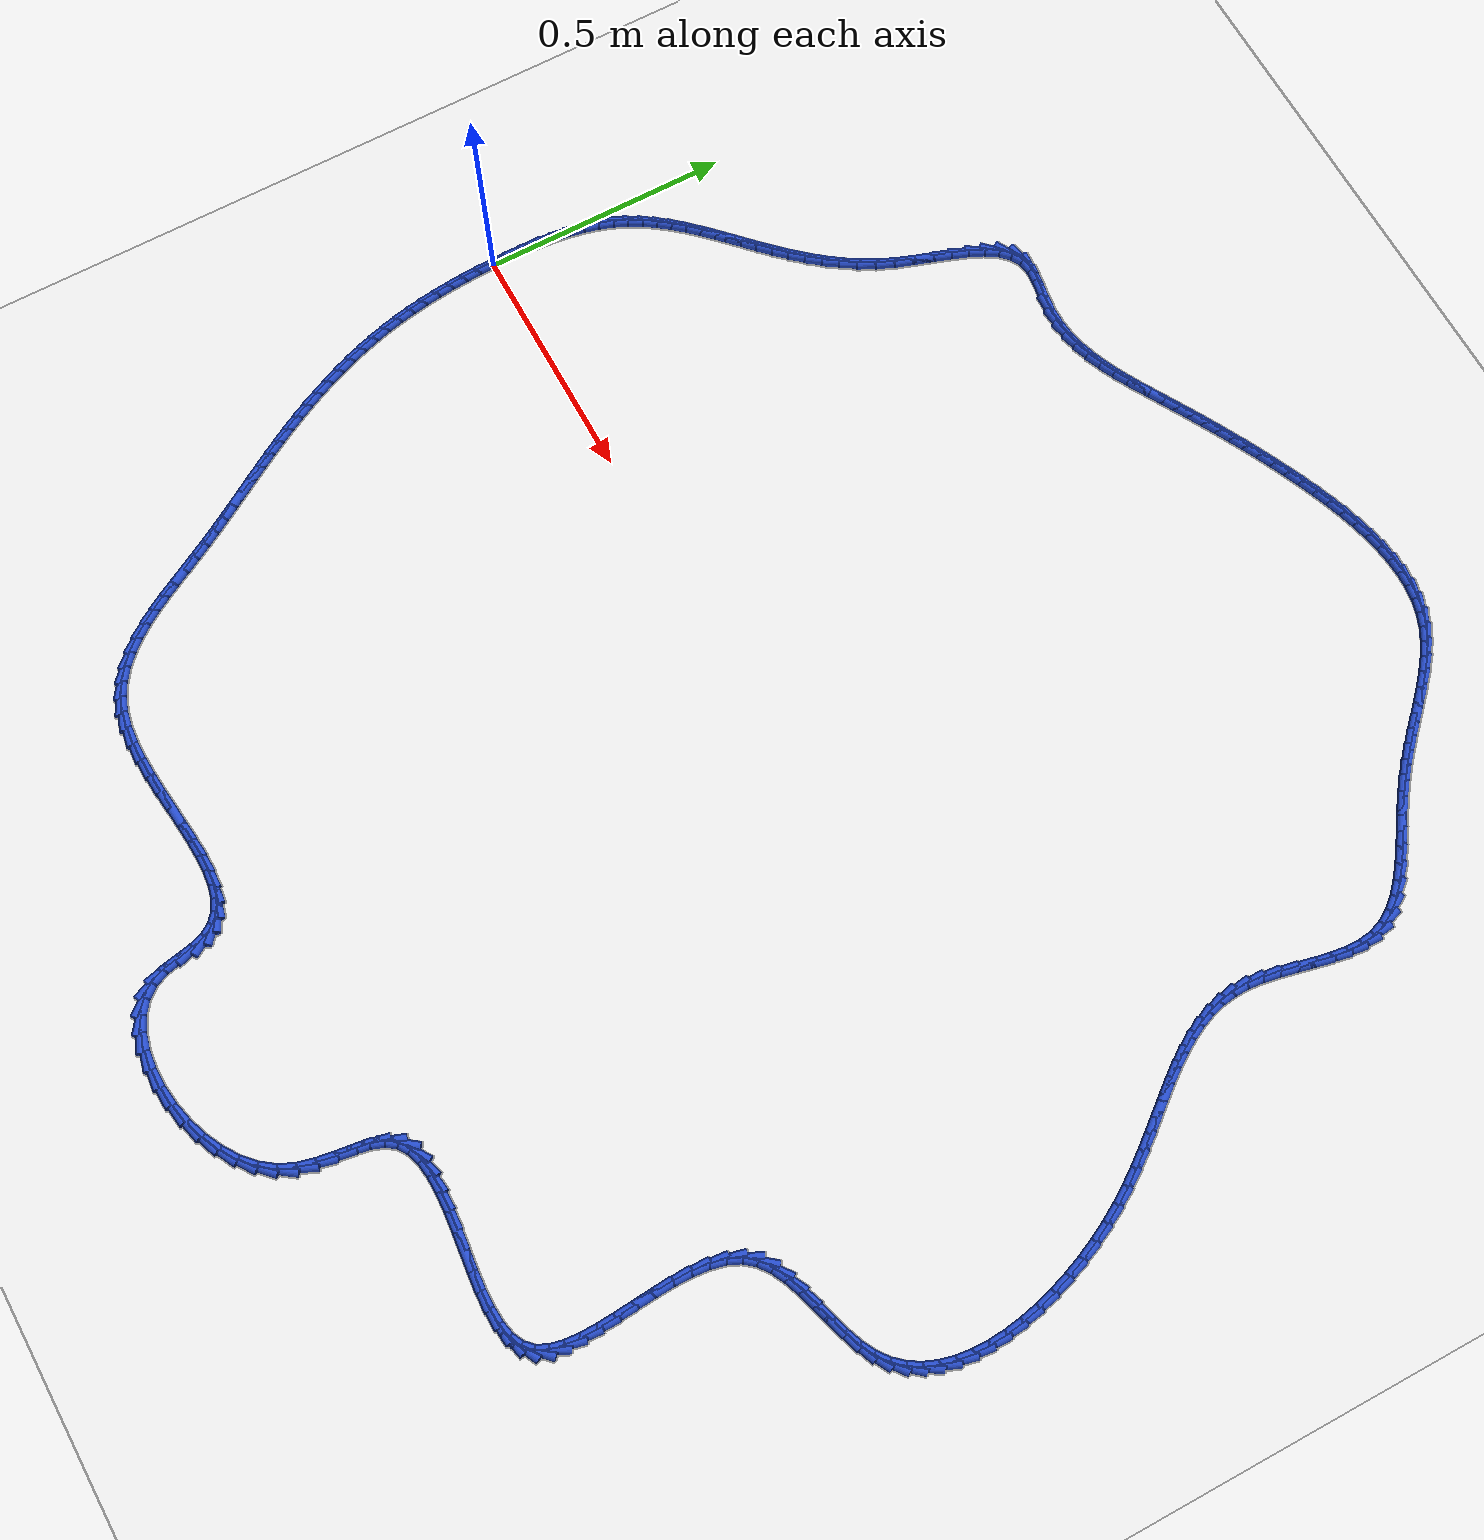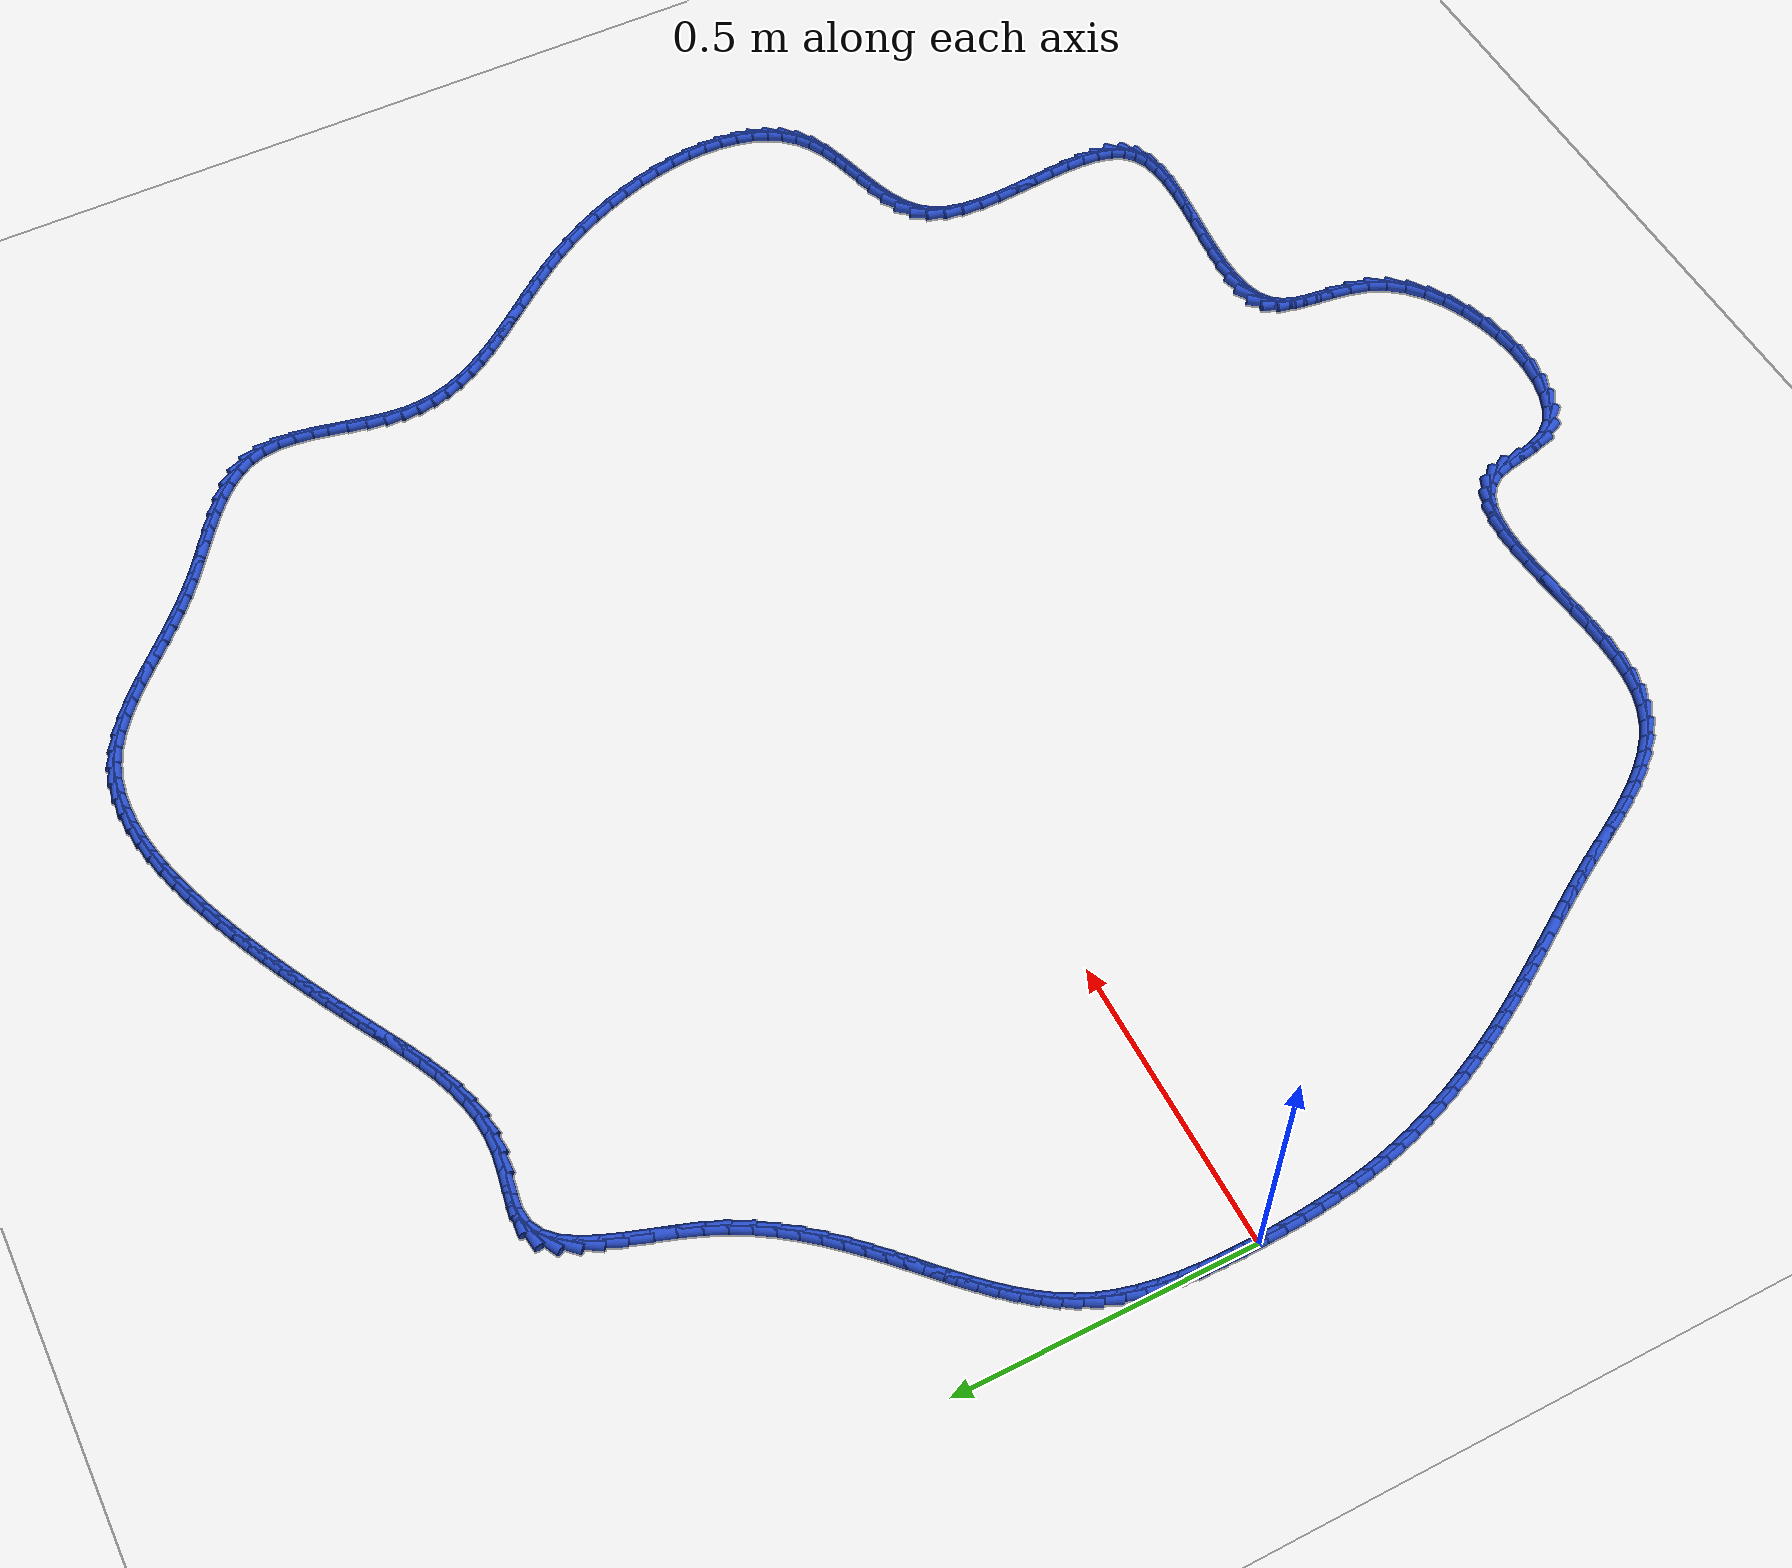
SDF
<sdf version="1.6">
 <world name="default">
  <light name="sun" type="directional">
   <pose>0 0 10 0 -0 0</pose>
   <diffuse>0.8 0.8 0.8 1</diffuse>
   <specular>0.2 0.2 0.2 1</specular>
   <attenuation>
    <range>1000</range>
    <constant>0.9</constant>
    <linear>0.01</linear>
    <quadratic>0.001</quadratic>
   </attenuation>
   <direction>-0.5 0.1 -0.9</direction>
  </light>
  <model name="ground_plane">
   <static>1</static>
   <link name="link">
    <collision name="collision">
     <geometry><plane><normal>0 0 1</normal><size>100 100</size></plane></geometry>
     <surface><friction><ode><mu>100</mu><mu2>50</mu2></ode></friction></surface>
    </collision>
    <visual name="visual">
     <cast_shadows>0</cast_shadows>
     <geometry><plane><normal>0 0 1</normal><size>100 100</size></plane></geometry>
     <material>
      <script><uri>file://media/materials/scripts/gazebo.material</uri><name>Gazebo/WhiteGlow</name></script>
     </material>
    </visual>
   </link>
  </model>
  <gravity>0 0 -9.8</gravity>
  <magnetic_field>6e-06 2.3e-05 -4.2e-05</magnetic_field>
  <atmosphere type="adiabatic"/>
  <physics name="default_physics" default="0" type="ode">
   <max_step_size>0.001</max_step_size>
   <real_time_factor>1</real_time_factor>
   <real_time_update_rate>1000</real_time_update_rate>
  </physics>
  <scene><ambient>0.4 0.4 0.4 1</ambient><background>0.7 0.7 0.7 1</background><shadows>1</shadows></scene>
  <spherical_coordinates>
   <surface_model>EARTH_WGS84</surface_model>
   <latitude_deg>0</latitude_deg>
   <longitude_deg>0</longitude_deg>
   <elevation>0</elevation>
   <heading_deg>0</heading_deg>
  </spherical_coordinates>
  <model name="line">
   <link name="link_0">
    <pose>-3.0357660829594124e-18 4.85722573273506e-17 0.01 0 1.57 -1.5546843273915216</pose>
    <collision name="collision">
     <geometry><cylinder><radius>0.01</radius><length>0.08</length></cylinder></geometry>
    </collision>
    <visual name="visual">
     <material>
      <script><name>Gazebo/Blue</name><uri>file://media/materials/scripts/gazebo.material</uri></script>
     </material>
     <geometry><cylinder><radius>0.01</radius><length>0.08</length></cylinder></geometry>
    </visual>
   </link>
   <link name="link_1">
    <pose>-0.0005251453368446715 0.032590610323636665 0.01 0 1.57 1.5620680607582746</pose>
    <collision name="collision">
     <geometry><cylinder><radius>0.01</radius><length>0.08</length></cylinder></geometry>
    </collision>
    <visual name="visual">
     <material>
      <script><name>Gazebo/Blue</name><uri>file://media/materials/scripts/gazebo.material</uri></script>
     </material>
     <geometry><cylinder><radius>0.01</radius><length>0.08</length></cylinder></geometry>
    </visual>
   </link>
   <link name="link_2">
    <pose>-0.00023959789321550533 0.0653050339150706 0.01 0 1.57 1.5304487570608454</pose>
    <collision name="collision">
     <geometry><cylinder><radius>0.01</radius><length>0.08</length></cylinder></geometry>
    </collision>
    <visual name="visual">
     <material>
      <script><name>Gazebo/Blue</name><uri>file://media/materials/scripts/gazebo.material</uri></script>
     </material>
     <geometry><cylinder><radius>0.01</radius><length>0.08</length></cylinder></geometry>
    </visual>
   </link>
   <link name="link_3">
    <pose>0.0010764351715110935 0.09790473845484757 0.01 0 1.57 1.4913794073407562</pose>
    <collision name="collision">
     <geometry><cylinder><radius>0.01</radius><length>0.08</length></cylinder></geometry>
    </collision>
    <visual name="visual">
     <material>
      <script><name>Gazebo/Blue</name><uri>file://media/materials/scripts/gazebo.material</uri></script>
     </material>
     <geometry><cylinder><radius>0.01</radius><length>0.08</length></cylinder></geometry>
    </visual>
   </link>
   <link name="link_4">
    <pose>0.0036427466979587287 0.13015119162351318 0.01 0 1.57 1.4439677340581123</pose>
    <collision name="collision">
     <geometry><cylinder><radius>0.01</radius><length>0.08</length></cylinder></geometry>
    </collision>
    <visual name="visual">
     <material>
      <script><name>Gazebo/Blue</name><uri>file://media/materials/scripts/gazebo.material</uri></script>
     </material>
     <geometry><cylinder><radius>0.01</radius><length>0.08</length></cylinder></geometry>
    </visual>
   </link>
   <link name="link_5">
    <pose>0.007679129526751 0.16180586110161316 0.01 0 1.57 1.3871199302643595</pose>
    <collision name="collision">
     <geometry><cylinder><radius>0.01</radius><length>0.08</length></cylinder></geometry>
    </collision>
    <visual name="visual">
     <material>
      <script><name>Gazebo/Blue</name><uri>file://media/materials/scripts/gazebo.material</uri></script>
     </material>
     <geometry><cylinder><radius>0.01</radius><length>0.08</length></cylinder></geometry>
    </visual>
   </link>
   <link name="link_6">
    <pose>0.013405376498511517 0.19263021456969318 0.01 0 1.57 1.3195953880795979</pose>
    <collision name="collision">
     <geometry><cylinder><radius>0.01</radius><length>0.08</length></cylinder></geometry>
    </collision>
    <visual name="visual">
     <material>
      <script><name>Gazebo/Blue</name><uri>file://media/materials/scripts/gazebo.material</uri></script>
     </material>
     <geometry><cylinder><radius>0.01</radius><length>0.08</length></cylinder></geometry>
    </visual>
   </link>
   <link name="link_7">
    <pose>0.021041280453863866 0.22238571970829885 0.01 0 1.57 1.2401306549969577</pose>
    <collision name="collision">
     <geometry><cylinder><radius>0.01</radius><length>0.08</length></cylinder></geometry>
    </collision>
    <visual name="visual">
     <material>
      <script><name>Gazebo/Blue</name><uri>file://media/materials/scripts/gazebo.material</uri></script>
     </material>
     <geometry><cylinder><radius>0.01</radius><length>0.08</length></cylinder></geometry>
    </visual>
   </link>
   <link name="link_8">
    <pose>0.030806634233431655 0.2508338441979757 0.01 0 1.57 1.1489375937324762</pose>
    <collision name="collision">
     <geometry><cylinder><radius>0.01</radius><length>0.08</length></cylinder></geometry>
    </collision>
    <visual name="visual">
     <material>
      <script><name>Gazebo/Blue</name><uri>file://media/materials/scripts/gazebo.material</uri></script>
     </material>
     <geometry><cylinder><radius>0.01</radius><length>0.08</length></cylinder></geometry>
    </visual>
   </link>
   <link name="link_9">
    <pose>0.042892854640813535 0.2777636963658499 0.01 0 1.57 1.0588721254618167</pose>
    <collision name="collision">
     <geometry><cylinder><radius>0.01</radius><length>0.08</length></cylinder></geometry>
    </collision>
    <visual name="visual">
     <material>
      <script><name>Gazebo/Blue</name><uri>file://media/materials/scripts/gazebo.material</uri></script>
     </material>
     <geometry><cylinder><radius>0.01</radius><length>0.08</length></cylinder></geometry>
    </visual>
   </link>
   <link name="link_10">
    <pose>0.057207935721278844 0.3032404621424432 0.01 0 1.57 0.9792647785890002</pose>
    <collision name="collision">
     <geometry><cylinder><radius>0.01</radius><length>0.08</length></cylinder></geometry>
    </collision>
    <visual name="visual">
     <material>
      <script><name>Gazebo/Blue</name><uri>file://media/materials/scripts/gazebo.material</uri></script>
     </material>
     <geometry><cylinder><radius>0.01</radius><length>0.08</length></cylinder></geometry>
    </visual>
   </link>
   <link name="link_11">
    <pose>0.07349690129972358 0.3274880741592514 0.01 0 1.57 0.911712006468641</pose>
    <collision name="collision">
     <geometry><cylinder><radius>0.01</radius><length>0.08</length></cylinder></geometry>
    </collision>
    <visual name="visual">
     <material>
      <script><name>Gazebo/Blue</name><uri>file://media/materials/scripts/gazebo.material</uri></script>
     </material>
     <geometry><cylinder><radius>0.01</radius><length>0.08</length></cylinder></geometry>
    </visual>
   </link>
   <link name="link_12">
    <pose>0.09150282722308628 0.35073236254213264 0.01 0 1.57 0.8568393463129899</pose>
    <collision name="collision">
     <geometry><cylinder><radius>0.01</radius><length>0.08</length></cylinder></geometry>
    </collision>
    <visual name="visual">
     <material>
      <script><name>Gazebo/Blue</name><uri>file://media/materials/scripts/gazebo.material</uri></script>
     </material>
     <geometry><cylinder><radius>0.01</radius><length>0.08</length></cylinder></geometry>
    </visual>
   </link>
   <link name="link_13">
    <pose>0.11096878933830527 0.37319915741694454 0.01 0 1.57 0.814650837585814</pose>
    <collision name="collision">
     <geometry><cylinder><radius>0.01</radius><length>0.08</length></cylinder></geometry>
    </collision>
    <visual name="visual">
     <material>
      <script><name>Gazebo/Blue</name><uri>file://media/materials/scripts/gazebo.material</uri></script>
     </material>
     <geometry><cylinder><radius>0.01</radius><length>0.08</length></cylinder></geometry>
    </visual>
   </link>
   <link name="link_14">
    <pose>0.131637863492319 0.3951142889095449 0.01 0 1.57 0.7847972129373869</pose>
    <collision name="collision">
     <geometry><cylinder><radius>0.01</radius><length>0.08</length></cylinder></geometry>
    </collision>
    <visual name="visual">
     <material>
      <script><name>Gazebo/Blue</name><uri>file://media/materials/scripts/gazebo.material</uri></script>
     </material>
     <geometry><cylinder><radius>0.01</radius><length>0.08</length></cylinder></geometry>
    </visual>
   </link>
   <link name="link_15">
    <pose>0.15325312553206605 0.4167035871457918 0.01 0 1.57 0.7667851147117307</pose>
    <collision name="collision">
     <geometry><cylinder><radius>0.01</radius><length>0.08</length></cylinder></geometry>
    </collision>
    <visual name="visual">
     <material>
      <script><name>Gazebo/Blue</name><uri>file://media/materials/scripts/gazebo.material</uri></script>
     </material>
     <geometry><cylinder><radius>0.01</radius><length>0.08</length></cylinder></geometry>
    </visual>
   </link>
   <link name="link_16">
    <pose>0.17555765130448472 0.43819288225154296 0.01 0 1.57 0.7601117168905399</pose>
    <collision name="collision">
     <geometry><cylinder><radius>0.01</radius><length>0.08</length></cylinder></geometry>
    </collision>
    <visual name="visual">
     <material>
      <script><name>Gazebo/Blue</name><uri>file://media/materials/scripts/gazebo.material</uri></script>
     </material>
     <geometry><cylinder><radius>0.01</radius><length>0.08</length></cylinder></geometry>
    </visual>
   </link>
   <link name="link_17">
    <pose>0.19829451665651351 0.459808004352656 0.01 0 1.57 0.7643335130624358</pose>
    <collision name="collision">
     <geometry><cylinder><radius>0.01</radius><length>0.08</length></cylinder></geometry>
    </collision>
    <visual name="visual">
     <material>
      <script><name>Gazebo/Blue</name><uri>file://media/materials/scripts/gazebo.material</uri></script>
     </material>
     <geometry><cylinder><radius>0.01</radius><length>0.08</length></cylinder></geometry>
    </visual>
   </link>
   <link name="link_18">
    <pose>0.22120679743509084 0.48177478357498915 0.01 0 1.57 0.7790840800480028</pose>
    <collision name="collision">
     <geometry><cylinder><radius>0.01</radius><length>0.08</length></cylinder></geometry>
    </collision>
    <visual name="visual">
     <material>
      <script><name>Gazebo/Blue</name><uri>file://media/materials/scripts/gazebo.material</uri></script>
     </material>
     <geometry><cylinder><radius>0.01</radius><length>0.08</length></cylinder></geometry>
    </visual>
   </link>
   <link name="link_19">
    <pose>0.24403756948715513 0.5043190500443998 0.01 0 1.57 0.8040532003164864</pose>
    <collision name="collision">
     <geometry><cylinder><radius>0.01</radius><length>0.08</length></cylinder></geometry>
    </collision>
    <visual name="visual">
     <material>
      <script><name>Gazebo/Blue</name><uri>file://media/materials/scripts/gazebo.material</uri></script>
     </material>
     <geometry><cylinder><radius>0.01</radius><length>0.08</length></cylinder></geometry>
    </visual>
   </link>
   <link name="link_20">
    <pose>0.2665299086596449 0.5276666338867463 0.01 0 1.57 0.8389356765060707</pose>
    <collision name="collision">
     <geometry><cylinder><radius>0.01</radius><length>0.08</length></cylinder></geometry>
    </collision>
    <visual name="visual">
     <material>
      <script><name>Gazebo/Blue</name><uri>file://media/materials/scripts/gazebo.material</uri></script>
     </material>
     <geometry><cylinder><radius>0.01</radius><length>0.08</length></cylinder></geometry>
    </visual>
   </link>
   <link name="link_21">
    <pose>0.28842689079949846 0.552043365227886 0.01 0 1.57 0.8833561399090529</pose>
    <collision name="collision">
     <geometry><cylinder><radius>0.01</radius><length>0.08</length></cylinder></geometry>
    </collision>
    <visual name="visual">
     <material>
      <script><name>Gazebo/Blue</name><uri>file://media/materials/scripts/gazebo.material</uri></script>
     </material>
     <geometry><cylinder><radius>0.01</radius><length>0.08</length></cylinder></geometry>
    </visual>
   </link>
   <link name="link_22">
    <pose>0.3094715917536544 0.5776750741936771 0.01 0 1.57 0.9367778790147734</pose>
    <collision name="collision">
     <geometry><cylinder><radius>0.01</radius><length>0.08</length></cylinder></geometry>
    </collision>
    <visual name="visual">
     <material>
      <script><name>Gazebo/Blue</name><uri>file://media/materials/scripts/gazebo.material</uri></script>
     </material>
     <geometry><cylinder><radius>0.01</radius><length>0.08</length></cylinder></geometry>
    </visual>
   </link>
   <link name="link_23">
    <pose>0.32940708736905105 0.6047875909099774 0.01 0 1.57 0.9984095267916203</pose>
    <collision name="collision">
     <geometry><cylinder><radius>0.01</radius><length>0.08</length></cylinder></geometry>
    </collision>
    <visual name="visual">
     <material>
      <script><name>Gazebo/Blue</name><uri>file://media/materials/scripts/gazebo.material</uri></script>
     </material>
     <geometry><cylinder><radius>0.01</radius><length>0.08</length></cylinder></geometry>
    </visual>
   </link>
   <link name="link_24">
    <pose>0.3479764534926272 0.6336067455026448 0.01 0 1.57 1.0671315954413565</pose>
    <collision name="collision">
     <geometry><cylinder><radius>0.01</radius><length>0.08</length></cylinder></geometry>
    </collision>
    <visual name="visual">
     <material>
      <script><name>Gazebo/Blue</name><uri>file://media/materials/scripts/gazebo.material</uri></script>
     </material>
     <geometry><cylinder><radius>0.01</radius><length>0.08</length></cylinder></geometry>
    </visual>
   </link>
   <link name="link_25">
    <pose>0.36492276597132045 0.6643583680975362 0.01 0 1.57 1.1413952239322365</pose>
    <collision name="collision">
     <geometry><cylinder><radius>0.01</radius><length>0.08</length></cylinder></geometry>
    </collision>
    <visual name="visual">
     <material>
      <script><name>Gazebo/Blue</name><uri>file://media/materials/scripts/gazebo.material</uri></script>
     </material>
     <geometry><cylinder><radius>0.01</radius><length>0.08</length></cylinder></geometry>
    </visual>
   </link>
   <link name="link_26">
    <pose>0.3799908967489671 0.6972656636821477 0.01 0 1.57 1.207326843936887</pose>
    <collision name="collision">
     <geometry><cylinder><radius>0.01</radius><length>0.08</length></cylinder></geometry>
    </collision>
    <visual name="visual">
     <material>
      <script><name>Gazebo/Blue</name><uri>file://media/materials/scripts/gazebo.material</uri></script>
     </material>
     <geometry><cylinder><radius>0.01</radius><length>0.08</length></cylinder></geometry>
    </visual>
   </link>
   <link name="link_27">
    <pose>0.3932386787956656 0.7320944198308803 0.01 0 1.57 1.2413150006009854</pose>
    <collision name="collision">
     <geometry><cylinder><radius>0.01</radius><length>0.08</length></cylinder></geometry>
    </collision>
    <visual name="visual">
     <material>
      <script><name>Gazebo/Blue</name><uri>file://media/materials/scripts/gazebo.material</uri></script>
     </material>
     <geometry><cylinder><radius>0.01</radius><length>0.08</length></cylinder></geometry>
    </visual>
   </link>
   <link name="link_28">
    <pose>0.4053915194729792 0.7676347110881909 0.01 0 1.57 1.2431237728315745</pose>
    <collision name="collision">
     <geometry><cylinder><radius>0.01</radius><length>0.08</length></cylinder></geometry>
    </collision>
    <visual name="visual">
     <material>
      <script><name>Gazebo/Blue</name><uri>file://media/materials/scripts/gazebo.material</uri></script>
     </material>
     <geometry><cylinder><radius>0.01</radius><length>0.08</length></cylinder></geometry>
    </visual>
   </link>
   <link name="link_29">
    <pose>0.41726058168269214 0.8025512734609088 0.01 0 1.57 1.2110322555889073</pose>
    <collision name="collision">
     <geometry><cylinder><radius>0.01</radius><length>0.08</length></cylinder></geometry>
    </collision>
    <visual name="visual">
     <material>
      <script><name>Gazebo/Blue</name><uri>file://media/materials/scripts/gazebo.material</uri></script>
     </material>
     <geometry><cylinder><radius>0.01</radius><length>0.08</length></cylinder></geometry>
    </visual>
   </link>
   <link name="link_30">
    <pose>0.429657028326589 0.8355088429558638 0.01 0 1.57 1.1371599077945795</pose>
    <collision name="collision">
     <geometry><cylinder><radius>0.01</radius><length>0.08</length></cylinder></geometry>
    </collision>
    <visual name="visual">
     <material>
      <script><name>Gazebo/Blue</name><uri>file://media/materials/scripts/gazebo.material</uri></script>
     </material>
     <geometry><cylinder><radius>0.01</radius><length>0.08</length></cylinder></geometry>
    </visual>
   </link>
   <link name="link_31">
    <pose>0.44339202230645347 0.8651721555798839 0.01 0 1.57 1.0053729598017225</pose>
    <collision name="collision">
     <geometry><cylinder><radius>0.01</radius><length>0.08</length></cylinder></geometry>
    </collision>
    <visual name="visual">
     <material>
      <script><name>Gazebo/Blue</name><uri>file://media/materials/scripts/gazebo.material</uri></script>
     </material>
     <geometry><cylinder><radius>0.01</radius><length>0.08</length></cylinder></geometry>
    </visual>
   </link>
   <link name="link_32">
    <pose>0.4592767265240702 0.8902059473397996 0.01 0 1.57 0.7912910661827198</pose>
    <collision name="collision">
     <geometry><cylinder><radius>0.01</radius><length>0.08</length></cylinder></geometry>
    </collision>
    <visual name="visual">
     <material>
      <script><name>Gazebo/Blue</name><uri>file://media/materials/scripts/gazebo.material</uri></script>
     </material>
     <geometry><cylinder><radius>0.01</radius><length>0.08</length></cylinder></geometry>
    </visual>
   </link>
   <link name="link_33">
    <pose>0.47812230388122345 0.9092749542424399 0.01 0 1.57 0.4797906827714459</pose>
    <collision name="collision">
     <geometry><cylinder><radius>0.01</radius><length>0.08</length></cylinder></geometry>
    </collision>
    <visual name="visual">
     <material>
      <script><name>Gazebo/Blue</name><uri>file://media/materials/scripts/gazebo.material</uri></script>
     </material>
     <geometry><cylinder><radius>0.01</radius><length>0.08</length></cylinder></geometry>
    </visual>
   </link>
   <link name="link_34">
    <pose>0.5007399172796971 0.9210439122946334 0.01 0 1.57 0.12772534868190275</pose>
    <collision name="collision">
     <geometry><cylinder><radius>0.01</radius><length>0.08</length></cylinder></geometry>
    </collision>
    <visual name="visual">
     <material>
      <script><name>Gazebo/Blue</name><uri>file://media/materials/scripts/gazebo.material</uri></script>
     </material>
     <geometry><cylinder><radius>0.01</radius><length>0.08</length></cylinder></geometry>
    </visual>
   </link>
   <link name="link_35">
    <pose>0.527779397697808 0.9245164432795403 0.01 0 1.57 -0.09152931242597868</pose>
    <collision name="collision">
     <geometry><cylinder><radius>0.01</radius><length>0.08</length></cylinder></geometry>
    </collision>
    <visual name="visual">
     <material>
      <script><name>Gazebo/Blue</name><uri>file://media/materials/scripts/gazebo.material</uri></script>
     </material>
     <geometry><cylinder><radius>0.01</radius><length>0.08</length></cylinder></geometry>
    </visual>
   </link>
   <link name="link_36">
    <pose>0.5584603808973575 0.9217003655821675 0.01 0 1.57 -0.16695197239894577</pose>
    <collision name="collision">
     <geometry><cylinder><radius>0.01</radius><length>0.08</length></cylinder></geometry>
    </collision>
    <visual name="visual">
     <material>
      <script><name>Gazebo/Blue</name><uri>file://media/materials/scripts/gazebo.material</uri></script>
     </material>
     <geometry><cylinder><radius>0.01</radius><length>0.08</length></cylinder></geometry>
    </visual>
   </link>
   <link name="link_37">
    <pose>0.5912549316734963 0.9161738078023254 0.01 0 1.57 -0.13829959741874712</pose>
    <collision name="collision">
     <geometry><cylinder><radius>0.01</radius><length>0.08</length></cylinder></geometry>
    </collision>
    <visual name="visual">
     <material>
      <script><name>Gazebo/Blue</name><uri>file://media/materials/scripts/gazebo.material</uri></script>
     </material>
     <geometry><cylinder><radius>0.01</radius><length>0.08</length></cylinder></geometry>
    </visual>
   </link>
   <link name="link_38">
    <pose>0.6246285966978147 0.911528589511543 0.01 0 1.57 -0.02734627377530669</pose>
    <collision name="collision">
     <geometry><cylinder><radius>0.01</radius><length>0.08</length></cylinder></geometry>
    </collision>
    <visual name="visual">
     <material>
      <script><name>Gazebo/Blue</name><uri>file://media/materials/scripts/gazebo.material</uri></script>
     </material>
     <geometry><cylinder><radius>0.01</radius><length>0.08</length></cylinder></geometry>
    </visual>
   </link>
   <link name="link_39">
    <pose>0.6573288925218297 0.9106341352950962 0.01 0 1.57 0.09345466645163591</pose>
    <collision name="collision">
     <geometry><cylinder><radius>0.01</radius><length>0.08</length></cylinder></geometry>
    </collision>
    <visual name="visual">
     <material>
      <script><name>Gazebo/Blue</name><uri>file://media/materials/scripts/gazebo.material</uri></script>
     </material>
     <geometry><cylinder><radius>0.01</radius><length>0.08</length></cylinder></geometry>
    </visual>
   </link>
   <link name="link_40">
    <pose>0.6891732352585526 0.9136188320103223 0.01 0 1.57 0.20142658789239246</pose>
    <collision name="collision">
     <geometry><cylinder><radius>0.01</radius><length>0.08</length></cylinder></geometry>
    </collision>
    <visual name="visual">
     <material>
      <script><name>Gazebo/Blue</name><uri>file://media/materials/scripts/gazebo.material</uri></script>
     </material>
     <geometry><cylinder><radius>0.01</radius><length>0.08</length></cylinder></geometry>
    </visual>
   </link>
   <link name="link_41">
    <pose>0.7202327587477545 0.9199610523577911 0.01 0 1.57 0.2937035245050092</pose>
    <collision name="collision">
     <geometry><cylinder><radius>0.01</radius><length>0.08</length></cylinder></geometry>
    </collision>
    <visual name="visual">
     <material>
      <script><name>Gazebo/Blue</name><uri>file://media/materials/scripts/gazebo.material</uri></script>
     </material>
     <geometry><cylinder><radius>0.01</radius><length>0.08</length></cylinder></geometry>
    </visual>
   </link>
   <link name="link_42">
    <pose>0.7505785968292057 0.9291391690380713 0.01 0 1.57 0.36916790789140325</pose>
    <collision name="collision">
     <geometry><cylinder><radius>0.01</radius><length>0.08</length></cylinder></geometry>
    </collision>
    <visual name="visual">
     <material>
      <script><name>Gazebo/Blue</name><uri>file://media/materials/scripts/gazebo.material</uri></script>
     </material>
     <geometry><cylinder><radius>0.01</radius><length>0.08</length></cylinder></geometry>
    </visual>
   </link>
   <link name="link_43">
    <pose>0.780281883342677 0.9406315547517325 0.01 0 1.57 0.42785775329782727</pose>
    <collision name="collision">
     <geometry><cylinder><radius>0.01</radius><length>0.08</length></cylinder></geometry>
    </collision>
    <visual name="visual">
     <material>
      <script><name>Gazebo/Blue</name><uri>file://media/materials/scripts/gazebo.material</uri></script>
     </material>
     <geometry><cylinder><radius>0.01</radius><length>0.08</length></cylinder></geometry>
    </visual>
   </link>
   <link name="link_44">
    <pose>0.809413752127939 0.9539165821993436 0.01 0 1.57 0.47033790380012375</pose>
    <collision name="collision">
     <geometry><cylinder><radius>0.01</radius><length>0.08</length></cylinder></geometry>
    </collision>
    <visual name="visual">
     <material>
      <script><name>Gazebo/Blue</name><uri>file://media/materials/scripts/gazebo.material</uri></script>
     </material>
     <geometry><cylinder><radius>0.01</radius><length>0.08</length></cylinder></geometry>
    </visual>
   </link>
   <link name="link_45">
    <pose>0.8380453370247627 0.968472624081474 0.01 0 1.57 0.497220447050802</pose>
    <collision name="collision">
     <geometry><cylinder><radius>0.01</radius><length>0.08</length></cylinder></geometry>
    </collision>
    <visual name="visual">
     <material>
      <script><name>Gazebo/Blue</name><uri>file://media/materials/scripts/gazebo.material</uri></script>
     </material>
     <geometry><cylinder><radius>0.01</radius><length>0.08</length></cylinder></geometry>
    </visual>
   </link>
   <link name="link_46">
    <pose>0.8662477718729185 0.983778053098693 0.01 0 1.57 0.5088550428747309</pose>
    <collision name="collision">
     <geometry><cylinder><radius>0.01</radius><length>0.08</length></cylinder></geometry>
    </collision>
    <visual name="visual">
     <material>
      <script><name>Gazebo/Blue</name><uri>file://media/materials/scripts/gazebo.material</uri></script>
     </material>
     <geometry><cylinder><radius>0.01</radius><length>0.08</length></cylinder></geometry>
    </visual>
   </link>
   <link name="link_47">
    <pose>0.8940921905733983 0.9993112425939875 0.01 0 1.57 0.5075804313739977</pose>
    <collision name="collision">
     <geometry><cylinder><radius>0.01</radius><length>0.08</length></cylinder></geometry>
    </collision>
    <visual name="visual">
     <material>
      <script><name>Gazebo/Blue</name><uri>file://media/materials/scripts/gazebo.material</uri></script>
     </material>
     <geometry><cylinder><radius>0.01</radius><length>0.08</length></cylinder></geometry>
    </visual>
   </link>
   <link name="link_48">
    <pose>0.9216585628635784 1.0146432838042176 0.01 0 1.57 0.5023095526102133</pose>
    <collision name="collision">
     <geometry><cylinder><radius>0.01</radius><length>0.08</length></cylinder></geometry>
    </collision>
    <visual name="visual">
     <material>
      <script><name>Gazebo/Blue</name><uri>file://media/materials/scripts/gazebo.material</uri></script>
     </material>
     <geometry><cylinder><radius>0.01</radius><length>0.08</length></cylinder></geometry>
    </visual>
   </link>
   <link name="link_49">
    <pose>0.9490602009674362 1.0296951437448012 0.01 0 1.57 0.49518410823221304</pose>
    <collision name="collision">
     <geometry><cylinder><radius>0.01</radius><length>0.08</length></cylinder></geometry>
    </collision>
    <visual name="visual">
     <material>
      <script><name>Gazebo/Blue</name><uri>file://media/materials/scripts/gazebo.material</uri></script>
     </material>
     <geometry><cylinder><radius>0.01</radius><length>0.08</length></cylinder></geometry>
    </visual>
   </link>
   <link name="link_50">
    <pose>0.9764182805303183 1.0444703033931841 0.01 0 1.57 0.4862487569106676</pose>
    <collision name="collision">
     <geometry><cylinder><radius>0.01</radius><length>0.08</length></cylinder></geometry>
    </collision>
    <visual name="visual">
     <material>
      <script><name>Gazebo/Blue</name><uri>file://media/materials/scripts/gazebo.material</uri></script>
     </material>
     <geometry><cylinder><radius>0.01</radius><length>0.08</length></cylinder></geometry>
    </visual>
   </link>
   <link name="link_51">
    <pose>1.0038539771975703 1.0589722437268116 0.01 0 1.57 0.47558805553557737</pose>
    <collision name="collision">
     <geometry><cylinder><radius>0.01</radius><length>0.08</length></cylinder></geometry>
    </collision>
    <visual name="visual">
     <material>
      <script><name>Gazebo/Blue</name><uri>file://media/materials/scripts/gazebo.material</uri></script>
     </material>
     <geometry><cylinder><radius>0.01</radius><length>0.08</length></cylinder></geometry>
    </visual>
   </link>
   <link name="link_52">
    <pose>1.0314884666145394 1.0732044457231305 0.01 0 1.57 0.463324623906435</pose>
    <collision name="collision">
     <geometry><cylinder><radius>0.01</radius><length>0.08</length></cylinder></geometry>
    </collision>
    <visual name="visual">
     <material>
      <script><name>Gazebo/Blue</name><uri>file://media/materials/scripts/gazebo.material</uri></script>
     </material>
     <geometry><cylinder><radius>0.01</radius><length>0.08</length></cylinder></geometry>
    </visual>
   </link>
   <link name="link_53">
    <pose>1.0594429244265706 1.087170390359586 0.01 0 1.57 0.44961527726774564</pose>
    <collision name="collision">
     <geometry><cylinder><radius>0.01</radius><length>0.08</length></cylinder></geometry>
    </collision>
    <visual name="visual">
     <material>
      <script><name>Gazebo/Blue</name><uri>file://media/materials/scripts/gazebo.material</uri></script>
     </material>
     <geometry><cylinder><radius>0.01</radius><length>0.08</length></cylinder></geometry>
    </visual>
   </link>
   <link name="link_54">
    <pose>1.0878385262790107 1.1008735586136238 0.01 0 1.57 0.4346453161860608</pose>
    <collision name="collision">
     <geometry><cylinder><radius>0.01</radius><length>0.08</length></cylinder></geometry>
    </collision>
    <visual name="visual">
     <material>
      <script><name>Gazebo/Blue</name><uri>file://media/materials/scripts/gazebo.material</uri></script>
     </material>
     <geometry><cylinder><radius>0.01</radius><length>0.08</length></cylinder></geometry>
    </visual>
   </link>
   <link name="link_55">
    <pose>1.1167964478172054 1.1143174314626905 0.01 0 1.57 0.4186213511448961</pose>
    <collision name="collision">
     <geometry><cylinder><radius>0.01</radius><length>0.08</length></cylinder></geometry>
    </collision>
    <visual name="visual">
     <material>
      <script><name>Gazebo/Blue</name><uri>file://media/materials/scripts/gazebo.material</uri></script>
     </material>
     <geometry><cylinder><radius>0.01</radius><length>0.08</length></cylinder></geometry>
    </visual>
   </link>
   <link name="link_56">
    <pose>1.1464378646865014 1.1275054898842312 0.01 0 1.57 0.40146732995015416</pose>
    <collision name="collision">
     <geometry><cylinder><radius>0.01</radius><length>0.08</length></cylinder></geometry>
    </collision>
    <visual name="visual">
     <material>
      <script><name>Gazebo/Blue</name><uri>file://media/materials/scripts/gazebo.material</uri></script>
     </material>
     <geometry><cylinder><radius>0.01</radius><length>0.08</length></cylinder></geometry>
    </visual>
   </link>
   <link name="link_57">
    <pose>1.1768653168603378 1.1404226710005245 0.01 0 1.57 0.38053230119687814</pose>
    <collision name="collision">
     <geometry><cylinder><radius>0.01</radius><length>0.08</length></cylinder></geometry>
    </collision>
    <visual name="visual">
     <material>
      <script><name>Gazebo/Blue</name><uri>file://media/materials/scripts/gazebo.material</uri></script>
     </material>
     <geometry><cylinder><radius>0.01</radius><length>0.08</length></cylinder></geometry>
    </visual>
   </link>
   <link name="link_58">
    <pose>1.2080067548952422 1.1528801827075925 0.01 0 1.57 0.35408981260244043</pose>
    <collision name="collision">
     <geometry><cylinder><radius>0.01</radius><length>0.08</length></cylinder></geometry>
    </collision>
    <visual name="visual">
     <material>
      <script><name>Gazebo/Blue</name><uri>file://media/materials/scripts/gazebo.material</uri></script>
     </material>
     <geometry><cylinder><radius>0.01</radius><length>0.08</length></cylinder></geometry>
    </visual>
   </link>
   <link name="link_59">
    <pose>1.2396946974499399 1.1645942711903865 0.01 0 1.57 0.3216742407927594</pose>
    <collision name="collision">
     <geometry><cylinder><radius>0.01</radius><length>0.08</length></cylinder></geometry>
    </collision>
    <visual name="visual">
     <material>
      <script><name>Gazebo/Blue</name><uri>file://media/materials/scripts/gazebo.material</uri></script>
     </material>
     <geometry><cylinder><radius>0.01</radius><length>0.08</length></cylinder></geometry>
    </visual>
   </link>
   <link name="link_60">
    <pose>1.2717606933681214 1.1752802175970374 0.01 0 1.57 0.28263354644725275</pose>
    <collision name="collision">
     <geometry><cylinder><radius>0.01</radius><length>0.08</length></cylinder></geometry>
    </collision>
    <visual name="visual">
     <material>
      <script><name>Gazebo/Blue</name><uri>file://media/materials/scripts/gazebo.material</uri></script>
     </material>
     <geometry><cylinder><radius>0.01</radius><length>0.08</length></cylinder></geometry>
    </visual>
   </link>
   <link name="link_61">
    <pose>1.304036291493478 1.1846533030756763 0.01 0 1.57 0.23611502922891736</pose>
    <collision name="collision">
     <geometry><cylinder><radius>0.01</radius><length>0.08</length></cylinder></geometry>
    </collision>
    <visual name="visual">
     <material>
      <script><name>Gazebo/Blue</name><uri>file://media/materials/scripts/gazebo.material</uri></script>
     </material>
     <geometry><cylinder><radius>0.01</radius><length>0.08</length></cylinder></geometry>
    </visual>
   </link>
   <link name="link_62">
    <pose>1.3363530406697008 1.192428808774435 0.01 0 1.57 0.181073547739236</pose>
    <collision name="collision">
     <geometry><cylinder><radius>0.01</radius><length>0.08</length></cylinder></geometry>
    </collision>
    <visual name="visual">
     <material>
      <script><name>Gazebo/Blue</name><uri>file://media/materials/scripts/gazebo.material</uri></script>
     </material>
     <geometry><cylinder><radius>0.01</radius><length>0.08</length></cylinder></geometry>
    </visual>
   </link>
   <link name="link_63">
    <pose>1.3685424897404819 1.1983220158414454 0.01 0 1.57 0.11630427548157742</pose>
    <collision name="collision">
     <geometry><cylinder><radius>0.01</radius><length>0.08</length></cylinder></geometry>
    </collision>
    <visual name="visual">
     <material>
      <script><name>Gazebo/Blue</name><uri>file://media/materials/scripts/gazebo.material</uri></script>
     </material>
     <geometry><cylinder><radius>0.01</radius><length>0.08</length></cylinder></geometry>
    </visual>
   </link>
   <link name="link_64">
    <pose>1.400436187549511 1.2020482054248378 0.01 0 1.57 0.04052739013193571</pose>
    <collision name="collision">
     <geometry><cylinder><radius>0.01</radius><length>0.08</length></cylinder></geometry>
    </collision>
    <visual name="visual">
     <material>
      <script><name>Gazebo/Blue</name><uri>file://media/materials/scripts/gazebo.material</uri></script>
     </material>
     <geometry><cylinder><radius>0.01</radius><length>0.08</length></cylinder></geometry>
    </visual>
   </link>
   <link name="link_65">
    <pose>1.4318656829404792 1.2033226586727446 0.01 0 1.57 -0.04743684946748167</pose>
    <collision name="collision">
     <geometry><cylinder><radius>0.01</radius><length>0.08</length></cylinder></geometry>
    </collision>
    <visual name="visual">
     <material>
      <script><name>Gazebo/Blue</name><uri>file://media/materials/scripts/gazebo.material</uri></script>
     </material>
     <geometry><cylinder><radius>0.01</radius><length>0.08</length></cylinder></geometry>
    </visual>
   </link>
   <link name="link_66">
    <pose>1.4626625247570788 1.2018606567332966 0.01 0 1.57 -0.14836221609609038</pose>
    <collision name="collision">
     <geometry><cylinder><radius>0.01</radius><length>0.08</length></cylinder></geometry>
    </collision>
    <visual name="visual">
     <material>
      <script><name>Gazebo/Blue</name><uri>file://media/materials/scripts/gazebo.material</uri></script>
     </material>
     <geometry><cylinder><radius>0.01</radius><length>0.08</length></cylinder></geometry>
    </visual>
   </link>
   <link name="link_67">
    <pose>1.492658261843 1.1973774807546256 0.01 0 1.57 -0.26216987482418747</pose>
    <collision name="collision">
     <geometry><cylinder><radius>0.01</radius><length>0.08</length></cylinder></geometry>
    </collision>
    <visual name="visual">
     <material>
      <script><name>Gazebo/Blue</name><uri>file://media/materials/scripts/gazebo.material</uri></script>
     </material>
     <geometry><cylinder><radius>0.01</radius><length>0.08</length></cylinder></geometry>
    </visual>
   </link>
   <link name="link_68">
    <pose>1.5216844430419334 1.1895884118848623 0.01 0 1.57 -0.3866303557922626</pose>
    <collision name="collision">
     <geometry><cylinder><radius>0.01</radius><length>0.08</length></cylinder></geometry>
    </collision>
    <visual name="visual">
     <material>
      <script><name>Gazebo/Blue</name><uri>file://media/materials/scripts/gazebo.material</uri></script>
     </material>
     <geometry><cylinder><radius>0.01</radius><length>0.08</length></cylinder></geometry>
    </visual>
   </link>
   <link name="link_69">
    <pose>1.5495805301013221 1.1782313192981213 0.01 0 1.57 -0.5034444426608695</pose>
    <collision name="collision">
     <geometry><cylinder><radius>0.01</radius><length>0.08</length></cylinder></geometry>
    </collision>
    <visual name="visual">
     <material>
      <script><name>Gazebo/Blue</name><uri>file://media/materials/scripts/gazebo.material</uri></script>
     </material>
     <geometry><cylinder><radius>0.01</radius><length>0.08</length></cylinder></geometry>
    </visual>
   </link>
   <link name="link_70">
    <pose>1.5763426215449061 1.1634912045594055 0.01 0 1.57 -0.597327470512749</pose>
    <collision name="collision">
     <geometry><cylinder><radius>0.01</radius><length>0.08</length></cylinder></geometry>
    </collision>
    <visual name="visual">
     <material>
      <script><name>Gazebo/Blue</name><uri>file://media/materials/scripts/gazebo.material</uri></script>
     </material>
     <geometry><cylinder><radius>0.01</radius><length>0.08</length></cylinder></geometry>
    </visual>
   </link>
   <link name="link_71">
    <pose>1.6021105385882406 1.1459633373223133 0.01 0 1.57 -0.6690885610182845</pose>
    <collision name="collision">
     <geometry><cylinder><radius>0.01</radius><length>0.08</length></cylinder></geometry>
    </collision>
    <visual name="visual">
     <material>
      <script><name>Gazebo/Blue</name><uri>file://media/materials/scripts/gazebo.material</uri></script>
     </material>
     <geometry><cylinder><radius>0.01</radius><length>0.08</length></cylinder></geometry>
    </visual>
   </link>
   <link name="link_72">
    <pose>1.6270294265378813 1.126258185290314 0.01 0 1.57 -0.7207876072355663</pose>
    <collision name="collision">
     <geometry><cylinder><radius>0.01</radius><length>0.08</length></cylinder></geometry>
    </collision>
    <visual name="visual">
     <material>
      <script><name>Gazebo/Blue</name><uri>file://media/materials/scripts/gazebo.material</uri></script>
     </material>
     <geometry><cylinder><radius>0.01</radius><length>0.08</length></cylinder></geometry>
    </visual>
   </link>
   <link name="link_73">
    <pose>1.6512444307003824 1.104986216166877 0.01 0 1.57 -0.7542877919329495</pose>
    <collision name="collision">
     <geometry><cylinder><radius>0.01</radius><length>0.08</length></cylinder></geometry>
    </collision>
    <visual name="visual">
     <material>
      <script><name>Gazebo/Blue</name><uri>file://media/materials/scripts/gazebo.material</uri></script>
     </material>
     <geometry><cylinder><radius>0.01</radius><length>0.08</length></cylinder></geometry>
    </visual>
   </link>
   <link name="link_74">
    <pose>1.6749006963823 1.0827578976554728 0.01 0 1.57 -0.770809108189896</pose>
    <collision name="collision">
     <geometry><cylinder><radius>0.01</radius><length>0.08</length></cylinder></geometry>
    </collision>
    <visual name="visual">
     <material>
      <script><name>Gazebo/Blue</name><uri>file://media/materials/scripts/gazebo.material</uri></script>
     </material>
     <geometry><cylinder><radius>0.01</radius><length>0.08</length></cylinder></geometry>
    </visual>
   </link>
   <link name="link_75">
    <pose>1.6981433688901884 1.0601836974595713 0.01 0 1.57 -0.7707226683922299</pose>
    <collision name="collision">
     <geometry><cylinder><radius>0.01</radius><length>0.08</length></cylinder></geometry>
    </collision>
    <visual name="visual">
     <material>
      <script><name>Gazebo/Blue</name><uri>file://media/materials/scripts/gazebo.material</uri></script>
     </material>
     <geometry><cylinder><radius>0.01</radius><length>0.08</length></cylinder></geometry>
    </visual>
   </link>
   <link name="link_76">
    <pose>1.7211175935306027 1.0378740832826423 0.01 0 1.57 -0.754811968397314</pose>
    <collision name="collision">
     <geometry><cylinder><radius>0.01</radius><length>0.08</length></cylinder></geometry>
    </collision>
    <visual name="visual">
     <material>
      <script><name>Gazebo/Blue</name><uri>file://media/materials/scripts/gazebo.material</uri></script>
     </material>
     <geometry><cylinder><radius>0.01</radius><length>0.08</length></cylinder></geometry>
    </visual>
   </link>
   <link name="link_77">
    <pose>1.7440060417106256 1.0163446334083515 0.01 0 1.57 -0.7297961062997002</pose>
    <collision name="collision">
     <geometry><cylinder><radius>0.01</radius><length>0.08</length></cylinder></geometry>
    </collision>
    <visual name="visual">
     <material>
      <script><name>Gazebo/Blue</name><uri>file://media/materials/scripts/gazebo.material</uri></script>
     </material>
     <geometry><cylinder><radius>0.01</radius><length>0.08</length></cylinder></geometry>
    </visual>
   </link>
   <link name="link_78">
    <pose>1.767192012695819 0.9956036135880233 0.01 0 1.57 -0.6988795385347634</pose>
    <collision name="collision">
     <geometry><cylinder><radius>0.01</radius><length>0.08</length></cylinder></geometry>
    </collision>
    <visual name="visual">
     <material>
      <script><name>Gazebo/Blue</name><uri>file://media/materials/scripts/gazebo.material</uri></script>
     </material>
     <geometry><cylinder><radius>0.01</radius><length>0.08</length></cylinder></geometry>
    </visual>
   </link>
   <link name="link_79">
    <pose>1.7911255777072876 0.9754904483656187 0.01 0 1.57 -0.6635041681701959</pose>
    <collision name="collision">
     <geometry><cylinder><radius>0.01</radius><length>0.08</length></cylinder></geometry>
    </collision>
    <visual name="visual">
     <material>
      <script><name>Gazebo/Blue</name><uri>file://media/materials/scripts/gazebo.material</uri></script>
     </material>
     <geometry><cylinder><radius>0.01</radius><length>0.08</length></cylinder></geometry>
    </visual>
   </link>
   <link name="link_80">
    <pose>1.8162568532088912 0.9558444478831588 0.01 0 1.57 -0.6268028935473543</pose>
    <collision name="collision">
     <geometry><cylinder><radius>0.01</radius><length>0.08</length></cylinder></geometry>
    </collision>
    <visual name="visual">
     <material>
      <script><name>Gazebo/Blue</name><uri>file://media/materials/scripts/gazebo.material</uri></script>
     </material>
     <geometry><cylinder><radius>0.01</radius><length>0.08</length></cylinder></geometry>
    </visual>
   </link>
   <link name="link_81">
    <pose>1.8429688313902335 0.9364988483295156 0.01 0 1.57 -0.6052456718027063</pose>
    <collision name="collision">
     <geometry><cylinder><radius>0.01</radius><length>0.08</length></cylinder></geometry>
    </collision>
    <visual name="visual">
     <material>
      <script><name>Gazebo/Blue</name><uri>file://media/materials/scripts/gazebo.material</uri></script>
     </material>
     <geometry><cylinder><radius>0.01</radius><length>0.08</length></cylinder></geometry>
    </visual>
   </link>
   <link name="link_82">
    <pose>1.8708421229488743 0.9172142798558062 0.01 0 1.57 -0.6071303076810874</pose>
    <collision name="collision">
     <geometry><cylinder><radius>0.01</radius><length>0.08</length></cylinder></geometry>
    </collision>
    <visual name="visual">
     <material>
      <script><name>Gazebo/Blue</name><uri>file://media/materials/scripts/gazebo.material</uri></script>
     </material>
     <geometry><cylinder><radius>0.01</radius><length>0.08</length></cylinder></geometry>
    </visual>
   </link>
   <link name="link_83">
    <pose>1.898929001017878 0.8977035643105689 0.01 0 1.57 -0.6321070335067361</pose>
    <collision name="collision">
     <geometry><cylinder><radius>0.01</radius><length>0.08</length></cylinder></geometry>
    </collision>
    <visual name="visual">
     <material>
      <script><name>Gazebo/Blue</name><uri>file://media/materials/scripts/gazebo.material</uri></script>
     </material>
     <geometry><cylinder><radius>0.01</radius><length>0.08</length></cylinder></geometry>
    </visual>
   </link>
   <link name="link_84">
    <pose>1.9262724409755136 0.8776786822054681 0.01 0 1.57 -0.6821321111519187</pose>
    <collision name="collision">
     <geometry><cylinder><radius>0.01</radius><length>0.08</length></cylinder></geometry>
    </collision>
    <visual name="visual">
     <material>
      <script><name>Gazebo/Blue</name><uri>file://media/materials/scripts/gazebo.material</uri></script>
     </material>
     <geometry><cylinder><radius>0.01</radius><length>0.08</length></cylinder></geometry>
    </visual>
   </link>
   <link name="link_85">
    <pose>1.9519154182000498 0.8568516140521687 0.01 0 1.57 -0.7616131077045573</pose>
    <collision name="collision">
     <geometry><cylinder><radius>0.01</radius><length>0.08</length></cylinder></geometry>
    </collision>
    <visual name="visual">
     <material>
      <script><name>Gazebo/Blue</name><uri>file://media/materials/scripts/gazebo.material</uri></script>
     </material>
     <geometry><cylinder><radius>0.01</radius><length>0.08</length></cylinder></geometry>
    </visual>
   </link>
   <link name="link_86">
    <pose>1.9749009080697542 0.834934340362336 0.01 0 1.57 -0.8771214338222975</pose>
    <collision name="collision">
     <geometry><cylinder><radius>0.01</radius><length>0.08</length></cylinder></geometry>
    </collision>
    <visual name="visual">
     <material>
      <script><name>Gazebo/Blue</name><uri>file://media/materials/scripts/gazebo.material</uri></script>
     </material>
     <geometry><cylinder><radius>0.01</radius><length>0.08</length></cylinder></geometry>
    </visual>
   </link>
   <link name="link_87">
    <pose>1.9942718859628958 0.8116388416476346 0.01 0 1.57 -1.0356249241007198</pose>
    <collision name="collision">
     <geometry><cylinder><radius>0.01</radius><length>0.08</length></cylinder></geometry>
    </collision>
    <visual name="visual">
     <material>
      <script><name>Gazebo/Blue</name><uri>file://media/materials/scripts/gazebo.material</uri></script>
     </material>
     <geometry><cylinder><radius>0.01</radius><length>0.08</length></cylinder></geometry>
    </visual>
   </link>
   <link name="link_88">
    <pose>2.0090713272577436 0.786677098419729 0.01 0 1.57 -1.238749753912228</pose>
    <collision name="collision">
     <geometry><cylinder><radius>0.01</radius><length>0.08</length></cylinder></geometry>
    </collision>
    <visual name="visual">
     <material>
      <script><name>Gazebo/Blue</name><uri>file://media/materials/scripts/gazebo.material</uri></script>
     </material>
     <geometry><cylinder><radius>0.01</radius><length>0.08</length></cylinder></geometry>
    </visual>
   </link>
   <link name="link_89">
    <pose>2.018351284087968 0.7597640975515839 0.01 0 1.57 -1.4481008485037783</pose>
    <collision name="collision">
     <geometry><cylinder><radius>0.01</radius><length>0.08</length></cylinder></geometry>
    </collision>
    <visual name="visual">
     <material>
      <script><name>Gazebo/Blue</name><uri>file://media/materials/scripts/gazebo.material</uri></script>
     </material>
     <geometry><cylinder><radius>0.01</radius><length>0.08</length></cylinder></geometry>
    </visual>
   </link>
   <link name="link_90">
    <pose>2.0219151365704913 0.7308636773253334 0.01 0 1.57 1.5364827264730359</pose>
    <collision name="collision">
     <geometry><cylinder><radius>0.01</radius><length>0.08</length></cylinder></geometry>
    </collision>
    <visual name="visual">
     <material>
      <script><name>Gazebo/Blue</name><uri>file://media/materials/scripts/gazebo.material</uri></script>
     </material>
     <geometry><cylinder><radius>0.01</radius><length>0.08</length></cylinder></geometry>
    </visual>
   </link>
   <link name="link_91">
    <pose>2.020868411047859 0.7003709669245711 0.01 0 1.57 1.4319663552815216</pose>
    <collision name="collision">
     <geometry><cylinder><radius>0.01</radius><length>0.08</length></cylinder></geometry>
    </collision>
    <visual name="visual">
     <material>
      <script><name>Gazebo/Blue</name><uri>file://media/materials/scripts/gazebo.material</uri></script>
     </material>
     <geometry><cylinder><radius>0.01</radius><length>0.08</length></cylinder></geometry>
    </visual>
   </link>
   <link name="link_92">
    <pose>2.0164464294721185 0.6687240858394529 0.01 0 1.57 1.3707481114223827</pose>
    <collision name="collision">
     <geometry><cylinder><radius>0.01</radius><length>0.08</length></cylinder></geometry>
    </collision>
    <visual name="visual">
     <material>
      <script><name>Gazebo/Blue</name><uri>file://media/materials/scripts/gazebo.material</uri></script>
     </material>
     <geometry><cylinder><radius>0.01</radius><length>0.08</length></cylinder></geometry>
    </visual>
   </link>
   <link name="link_93">
    <pose>2.0098845137953196 0.6363611535601353 0.01 0 1.57 1.3459174921613422</pose>
    <collision name="collision">
     <geometry><cylinder><radius>0.01</radius><length>0.08</length></cylinder></geometry>
    </collision>
    <visual name="visual">
     <material>
      <script><name>Gazebo/Blue</name><uri>file://media/materials/scripts/gazebo.material</uri></script>
     </material>
     <geometry><cylinder><radius>0.01</radius><length>0.08</length></cylinder></geometry>
    </visual>
   </link>
   <link name="link_94">
    <pose>2.0024179859695113 0.6037202895767755 0.01 0 1.57 1.3545376687539183</pose>
    <collision name="collision">
     <geometry><cylinder><radius>0.01</radius><length>0.08</length></cylinder></geometry>
    </collision>
    <visual name="visual">
     <material>
      <script><name>Gazebo/Blue</name><uri>file://media/materials/scripts/gazebo.material</uri></script>
     </material>
     <geometry><cylinder><radius>0.01</radius><length>0.08</length></cylinder></geometry>
    </visual>
   </link>
   <link name="link_95">
    <pose>1.9952821679467423 0.5712396133795297 0.01 0 1.57 1.3978436959004812</pose>
    <collision name="collision">
     <geometry><cylinder><radius>0.01</radius><length>0.08</length></cylinder></geometry>
    </collision>
    <visual name="visual">
     <material>
      <script><name>Gazebo/Blue</name><uri>file://media/materials/scripts/gazebo.material</uri></script>
     </material>
     <geometry><cylinder><radius>0.01</radius><length>0.08</length></cylinder></geometry>
    </visual>
   </link>
   <link name="link_96">
    <pose>1.9897123816790623 0.5393572444585538 0.01 0 1.57 1.481279869765003</pose>
    <collision name="collision">
     <geometry><cylinder><radius>0.01</radius><length>0.08</length></cylinder></geometry>
    </collision>
    <visual name="visual">
     <material>
      <script><name>Gazebo/Blue</name><uri>file://media/materials/scripts/gazebo.material</uri></script>
     </material>
     <geometry><cylinder><radius>0.01</radius><length>0.08</length></cylinder></geometry>
    </visual>
   </link>
   <link name="link_97">
    <pose>1.9869437560059244 0.508511223168112 0.01 0 1.57 -1.5393299501364148</pose>
    <collision name="collision">
     <geometry><cylinder><radius>0.01</radius><length>0.08</length></cylinder></geometry>
    </collision>
    <visual name="visual">
     <material>
      <script><name>Gazebo/Blue</name><uri>file://media/materials/scripts/gazebo.material</uri></script>
     </material>
     <geometry><cylinder><radius>0.01</radius><length>0.08</length></cylinder></geometry>
    </visual>
   </link>
   <link name="link_98">
    <pose>1.987872649799948 0.47900076482161813 0.01 0 1.57 -1.4135460609010608</pose>
    <collision name="collision">
     <geometry><cylinder><radius>0.01</radius><length>0.08</length></cylinder></geometry>
    </collision>
    <visual name="visual">
     <material>
      <script><name>Gazebo/Blue</name><uri>file://media/materials/scripts/gazebo.material</uri></script>
     </material>
     <geometry><cylinder><radius>0.01</radius><length>0.08</length></cylinder></geometry>
    </visual>
   </link>
   <link name="link_99">
    <pose>1.992359885082411 0.4507007305695978 0.01 0 1.57 -1.2955309220246773</pose>
    <collision name="collision">
     <geometry><cylinder><radius>0.01</radius><length>0.08</length></cylinder></geometry>
    </collision>
    <visual name="visual">
     <material>
      <script><name>Gazebo/Blue</name><uri>file://media/materials/scripts/gazebo.material</uri></script>
     </material>
     <geometry><cylinder><radius>0.01</radius><length>0.08</length></cylinder></geometry>
    </visual>
   </link>
   <link name="link_100">
    <pose>2.0000691083450444 0.42340518071355293 0.01 0 1.57 -1.1904182833578383</pose>
    <collision name="collision">
     <geometry><cylinder><radius>0.01</radius><length>0.08</length></cylinder></geometry>
    </collision>
    <visual name="visual">
     <material>
      <script><name>Gazebo/Blue</name><uri>file://media/materials/scripts/gazebo.material</uri></script>
     </material>
     <geometry><cylinder><radius>0.01</radius><length>0.08</length></cylinder></geometry>
    </visual>
   </link>
   <link name="link_101">
    <pose>2.0106639660795795 0.3969081755549869 0.01 0 1.57 -1.1012387039723956</pose>
    <collision name="collision">
     <geometry><cylinder><radius>0.01</radius><length>0.08</length></cylinder></geometry>
    </collision>
    <visual name="visual">
     <material>
      <script><name>Gazebo/Blue</name><uri>file://media/materials/scripts/gazebo.material</uri></script>
     </material>
     <geometry><cylinder><radius>0.01</radius><length>0.08</length></cylinder></geometry>
    </visual>
   </link>
   <link name="link_102">
    <pose>2.0238081047777476 0.3710037753954017 0.01 0 1.57 -1.0290401558910005</pose>
    <collision name="collision">
     <geometry><cylinder><radius>0.01</radius><length>0.08</length></cylinder></geometry>
    </collision>
    <visual name="visual">
     <material>
      <script><name>Gazebo/Blue</name><uri>file://media/materials/scripts/gazebo.material</uri></script>
     </material>
     <geometry><cylinder><radius>0.01</radius><length>0.08</length></cylinder></geometry>
    </visual>
   </link>
   <link name="link_103">
    <pose>2.0391651709312777 0.34548604053629944 0.01 0 1.57 -0.9734989373845796</pose>
    <collision name="collision">
     <geometry><cylinder><radius>0.01</radius><length>0.08</length></cylinder></geometry>
    </collision>
    <visual name="visual">
     <material>
      <script><name>Gazebo/Blue</name><uri>file://media/materials/scripts/gazebo.material</uri></script>
     </material>
     <geometry><cylinder><radius>0.01</radius><length>0.08</length></cylinder></geometry>
    </visual>
   </link>
   <link name="link_104">
    <pose>2.056398811031904 0.3201490312791825 0.01 0 1.57 -0.9335778565058855</pose>
    <collision name="collision">
     <geometry><cylinder><radius>0.01</radius><length>0.08</length></cylinder></geometry>
    </collision>
    <visual name="visual">
     <material>
      <script><name>Gazebo/Blue</name><uri>file://media/materials/scripts/gazebo.material</uri></script>
     </material>
     <geometry><cylinder><radius>0.01</radius><length>0.08</length></cylinder></geometry>
    </visual>
   </link>
   <link name="link_105">
    <pose>2.0751726715713557 0.29478680792555384 0.01 0 1.57 -0.9080083345994701</pose>
    <collision name="collision">
     <geometry><cylinder><radius>0.01</radius><length>0.08</length></cylinder></geometry>
    </collision>
    <visual name="visual">
     <material>
      <script><name>Gazebo/Blue</name><uri>file://media/materials/scripts/gazebo.material</uri></script>
     </material>
     <geometry><cylinder><radius>0.01</radius><length>0.08</length></cylinder></geometry>
    </visual>
   </link>
   <link name="link_106">
    <pose>2.095150399041363 0.26919343077691554 0.01 0 1.57 -0.8955668337158125</pose>
    <collision name="collision">
     <geometry><cylinder><radius>0.01</radius><length>0.08</length></cylinder></geometry>
    </collision>
    <visual name="visual">
     <material>
      <script><name>Gazebo/Blue</name><uri>file://media/materials/scripts/gazebo.material</uri></script>
     </material>
     <geometry><cylinder><radius>0.01</radius><length>0.08</length></cylinder></geometry>
    </visual>
   </link>
   <link name="link_107">
    <pose>2.115995639933659 0.24316296013476998 0.01 0 1.57 -0.8951964913153772</pose>
    <collision name="collision">
     <geometry><cylinder><radius>0.01</radius><length>0.08</length></cylinder></geometry>
    </collision>
    <visual name="visual">
     <material>
      <script><name>Gazebo/Blue</name><uri>file://media/materials/scripts/gazebo.material</uri></script>
     </material>
     <geometry><cylinder><radius>0.01</radius><length>0.08</length></cylinder></geometry>
    </visual>
   </link>
   <link name="link_108">
    <pose>2.1373720407399723 0.21648945630061922 0.01 0 1.57 -0.9060322694759152</pose>
    <collision name="collision">
     <geometry><cylinder><radius>0.01</radius><length>0.08</length></cylinder></geometry>
    </collision>
    <visual name="visual">
     <material>
      <script><name>Gazebo/Blue</name><uri>file://media/materials/scripts/gazebo.material</uri></script>
     </material>
     <geometry><cylinder><radius>0.01</radius><length>0.08</length></cylinder></geometry>
    </visual>
   </link>
   <link name="link_109">
    <pose>2.158943247952036 0.18896697957596637 0.01 0 1.57 -0.9273709605185472</pose>
    <collision name="collision">
     <geometry><cylinder><radius>0.01</radius><length>0.08</length></cylinder></geometry>
    </collision>
    <visual name="visual">
     <material>
      <script><name>Gazebo/Blue</name><uri>file://media/materials/scripts/gazebo.material</uri></script>
     </material>
     <geometry><cylinder><radius>0.01</radius><length>0.08</length></cylinder></geometry>
    </visual>
   </link>
   <link name="link_110">
    <pose>2.18037290806158 0.16038959026231348 0.01 0 1.57 -0.9586100523063572</pose>
    <collision name="collision">
     <geometry><cylinder><radius>0.01</radius><length>0.08</length></cylinder></geometry>
    </collision>
    <visual name="visual">
     <material>
      <script><name>Gazebo/Blue</name><uri>file://media/materials/scripts/gazebo.material</uri></script>
     </material>
     <geometry><cylinder><radius>0.01</radius><length>0.08</length></cylinder></geometry>
    </visual>
   </link>
   <link name="link_111">
    <pose>2.2013246675603355 0.13055134866116294 0.01 0 1.57 -0.9991686601985323</pose>
    <collision name="collision">
     <geometry><cylinder><radius>0.01</radius><length>0.08</length></cylinder></geometry>
    </collision>
    <visual name="visual">
     <material>
      <script><name>Gazebo/Blue</name><uri>file://media/materials/scripts/gazebo.material</uri></script>
     </material>
     <geometry><cylinder><radius>0.01</radius><length>0.08</length></cylinder></geometry>
    </visual>
   </link>
   <link name="link_112">
    <pose>2.221462172940034 0.09924631507401671 0.01 0 1.57 -1.0474736983022641</pose>
    <collision name="collision">
     <geometry><cylinder><radius>0.01</radius><length>0.08</length></cylinder></geometry>
    </collision>
    <visual name="visual">
     <material>
      <script><name>Gazebo/Blue</name><uri>file://media/materials/scripts/gazebo.material</uri></script>
     </material>
     <geometry><cylinder><radius>0.01</radius><length>0.08</length></cylinder></geometry>
    </visual>
   </link>
   <link name="link_113">
    <pose>2.240460815701075 0.06631870481339791 0.01 0 1.57 -1.0969140585130086</pose>
    <collision name="collision">
     <geometry><cylinder><radius>0.01</radius><length>0.08</length></cylinder></geometry>
    </collision>
    <visual name="visual">
     <material>
      <script><name>Gazebo/Blue</name><uri>file://media/materials/scripts/gazebo.material</uri></script>
     </material>
     <geometry><cylinder><radius>0.01</radius><length>0.08</length></cylinder></geometry>
    </visual>
   </link>
   <link name="link_114">
    <pose>2.2580787810658816 0.03196628934130513 0.01 0 1.57 -1.1458618231699673</pose>
    <collision name="collision">
     <geometry><cylinder><radius>0.01</radius><length>0.08</length></cylinder></geometry>
    </collision>
    <visual name="visual">
     <material>
      <script><name>Gazebo/Blue</name><uri>file://media/materials/scripts/gazebo.material</uri></script>
     </material>
     <geometry><cylinder><radius>0.01</radius><length>0.08</length></cylinder></geometry>
    </visual>
   </link>
   <link name="link_115">
    <pose>2.274109849896459 -0.003461154909834302 0.01 0 1.57 -1.1956128650950983</pose>
    <collision name="collision">
     <geometry><cylinder><radius>0.01</radius><length>0.08</length></cylinder></geometry>
    </collision>
    <visual name="visual">
     <material>
      <script><name>Gazebo/Blue</name><uri>file://media/materials/scripts/gazebo.material</uri></script>
     </material>
     <geometry><cylinder><radius>0.01</radius><length>0.08</length></cylinder></geometry>
    </visual>
   </link>
   <link name="link_116">
    <pose>2.288347940974419 -0.03961326254596081 0.01 0 1.57 -1.247480403172895</pose>
    <collision name="collision">
     <geometry><cylinder><radius>0.01</radius><length>0.08</length></cylinder></geometry>
    </collision>
    <visual name="visual">
     <material>
      <script><name>Gazebo/Blue</name><uri>file://media/materials/scripts/gazebo.material</uri></script>
     </material>
     <geometry><cylinder><radius>0.01</radius><length>0.08</length></cylinder></geometry>
    </visual>
   </link>
   <link name="link_117">
    <pose>2.3005869730813737 -0.07613966817301628 0.01 0 1.57 -1.3028740549496942</pose>
    <collision name="collision">
     <geometry><cylinder><radius>0.01</radius><length>0.08</length></cylinder></geometry>
    </collision>
    <visual name="visual">
     <material>
      <script><name>Gazebo/Blue</name><uri>file://media/materials/scripts/gazebo.material</uri></script>
     </material>
     <geometry><cylinder><radius>0.01</radius><length>0.08</length></cylinder></geometry>
    </visual>
   </link>
   <link name="link_118">
    <pose>2.3106208649989353 -0.11269000639694221 0.01 0 1.57 -1.363390371639965</pose>
    <collision name="collision">
     <geometry><cylinder><radius>0.01</radius><length>0.08</length></cylinder></geometry>
    </collision>
    <visual name="visual">
     <material>
      <script><name>Gazebo/Blue</name><uri>file://media/materials/scripts/gazebo.material</uri></script>
     </material>
     <geometry><cylinder><radius>0.01</radius><length>0.08</length></cylinder></geometry>
    </visual>
   </link>
   <link name="link_119">
    <pose>2.3182435355087145 -0.1489139118236804 0.01 0 1.57 -1.4309066042289407</pose>
    <collision name="collision">
     <geometry><cylinder><radius>0.01</radius><length>0.08</length></cylinder></geometry>
    </collision>
    <visual name="visual">
     <material>
      <script><name>Gazebo/Blue</name><uri>file://media/materials/scripts/gazebo.material</uri></script>
     </material>
     <geometry><cylinder><radius>0.01</radius><length>0.08</length></cylinder></geometry>
    </visual>
   </link>
   <link name="link_120">
    <pose>2.323248903392325 -0.18446101905917145 0.01 0 1.57 -1.5076709340313417</pose>
    <collision name="collision">
     <geometry><cylinder><radius>0.01</radius><length>0.08</length></cylinder></geometry>
    </collision>
    <visual name="visual">
     <material>
      <script><name>Gazebo/Blue</name><uri>file://media/materials/scripts/gazebo.material</uri></script>
     </material>
     <geometry><cylinder><radius>0.01</radius><length>0.08</length></cylinder></geometry>
    </visual>
   </link>
   <link name="link_121">
    <pose>2.3254308874313785 -0.21898096270935732 0.01 0 1.57 1.5452310084409746</pose>
    <collision name="collision">
     <geometry><cylinder><radius>0.01</radius><length>0.08</length></cylinder></geometry>
    </collision>
    <visual name="visual">
     <material>
      <script><name>Gazebo/Blue</name><uri>file://media/materials/scripts/gazebo.material</uri></script>
     </material>
     <geometry><cylinder><radius>0.01</radius><length>0.08</length></cylinder></geometry>
    </visual>
   </link>
   <link name="link_122">
    <pose>2.3245834064074855 -0.2521233773801792 0.01 0 1.57 1.4415482541909135</pose>
    <collision name="collision">
     <geometry><cylinder><radius>0.01</radius><length>0.08</length></cylinder></geometry>
    </collision>
    <visual name="visual">
     <material>
      <script><name>Gazebo/Blue</name><uri>file://media/materials/scripts/gazebo.material</uri></script>
     </material>
     <geometry><cylinder><radius>0.01</radius><length>0.08</length></cylinder></geometry>
    </visual>
   </link>
   <link name="link_123">
    <pose>2.32050037910226 -0.2835378976775788 0.01 0 1.57 1.3197125057567527</pose>
    <collision name="collision">
     <geometry><cylinder><radius>0.01</radius><length>0.08</length></cylinder></geometry>
    </collision>
    <visual name="visual">
     <material>
      <script><name>Gazebo/Blue</name><uri>file://media/materials/scripts/gazebo.material</uri></script>
     </material>
     <geometry><cylinder><radius>0.01</radius><length>0.08</length></cylinder></geometry>
    </visual>
   </link>
   <link name="link_124">
    <pose>2.312975724297313 -0.3128741582074974 0.01 0 1.57 1.1772456296817322</pose>
    <collision name="collision">
     <geometry><cylinder><radius>0.01</radius><length>0.08</length></cylinder></geometry>
    </collision>
    <visual name="visual">
     <material>
      <script><name>Gazebo/Blue</name><uri>file://media/materials/scripts/gazebo.material</uri></script>
     </material>
     <geometry><cylinder><radius>0.01</radius><length>0.08</length></cylinder></geometry>
    </visual>
   </link>
   <link name="link_125">
    <pose>2.301803360774256 -0.3397817935758771 0.01 0 1.57 1.0138154337687741</pose>
    <collision name="collision">
     <geometry><cylinder><radius>0.01</radius><length>0.08</length></cylinder></geometry>
    </collision>
    <visual name="visual">
     <material>
      <script><name>Gazebo/Blue</name><uri>file://media/materials/scripts/gazebo.material</uri></script>
     </material>
     <geometry><cylinder><radius>0.01</radius><length>0.08</length></cylinder></geometry>
    </visual>
   </link>
   <link name="link_126">
    <pose>2.2867772073147026 -0.3639104383886581 0.01 0 1.57 0.8330917742112157</pose>
    <collision name="collision">
     <geometry><cylinder><radius>0.01</radius><length>0.08</length></cylinder></geometry>
    </collision>
    <visual name="visual">
     <material>
      <script><name>Gazebo/Blue</name><uri>file://media/materials/scripts/gazebo.material</uri></script>
     </material>
     <geometry><cylinder><radius>0.01</radius><length>0.08</length></cylinder></geometry>
    </visual>
   </link>
   <link name="link_127">
    <pose>2.2676911827002635 -0.38490972725178235 0.01 0 1.57 0.6436708293450373</pose>
    <collision name="collision">
     <geometry><cylinder><radius>0.01</radius><length>0.08</length></cylinder></geometry>
    </collision>
    <visual name="visual">
     <material>
      <script><name>Gazebo/Blue</name><uri>file://media/materials/scripts/gazebo.material</uri></script>
     </material>
     <geometry><cylinder><radius>0.01</radius><length>0.08</length></cylinder></geometry>
    </visual>
   </link>
   <link name="link_128">
    <pose>2.244339561619305 -0.4024296364290641 0.01 0 1.57 0.47119744795232194</pose>
    <collision name="collision">
     <geometry><cylinder><radius>0.01</radius><length>0.08</length></cylinder></geometry>
    </collision>
    <visual name="visual">
     <material>
      <script><name>Gazebo/Blue</name><uri>file://media/materials/scripts/gazebo.material</uri></script>
     </material>
     <geometry><cylinder><radius>0.01</radius><length>0.08</length></cylinder></geometry>
    </visual>
   </link>
   <link name="link_129">
    <pose>2.2168463632862547 -0.4164366852452078 0.01 0 1.57 0.3558813686047044</pose>
    <collision name="collision">
     <geometry><cylinder><radius>0.01</radius><length>0.08</length></cylinder></geometry>
    </collision>
    <visual name="visual">
     <material>
      <script><name>Gazebo/Blue</name><uri>file://media/materials/scripts/gazebo.material</uri></script>
     </material>
     <geometry><cylinder><radius>0.01</radius><length>0.08</length></cylinder></geometry>
    </visual>
   </link>
   <link name="link_130">
    <pose>2.1862758461998175 -0.427799989421496 0.01 0 1.57 0.2921180129583744</pose>
    <collision name="collision">
     <geometry><cylinder><radius>0.01</radius><length>0.08</length></cylinder></geometry>
    </collision>
    <visual name="visual">
     <material>
      <script><name>Gazebo/Blue</name><uri>file://media/materials/scripts/gazebo.material</uri></script>
     </material>
     <geometry><cylinder><radius>0.01</radius><length>0.08</length></cylinder></geometry>
    </visual>
   </link>
   <link name="link_131">
    <pose>2.1538587548847588 -0.4375484853649836 0.01 0 1.57 0.27057619316791276</pose>
    <collision name="collision">
     <geometry><cylinder><radius>0.01</radius><length>0.08</length></cylinder></geometry>
    </collision>
    <visual name="visual">
     <material>
      <script><name>Gazebo/Blue</name><uri>file://media/materials/scripts/gazebo.material</uri></script>
     </material>
     <geometry><cylinder><radius>0.01</radius><length>0.08</length></cylinder></geometry>
    </visual>
   </link>
   <link name="link_132">
    <pose>2.1208258338658434 -0.446711109482726 0.01 0 1.57 0.2880654722294983</pose>
    <collision name="collision">
     <geometry><cylinder><radius>0.01</radius><length>0.08</length></cylinder></geometry>
    </collision>
    <visual name="visual">
     <material>
      <script><name>Gazebo/Blue</name><uri>file://media/materials/scripts/gazebo.material</uri></script>
     </material>
     <geometry><cylinder><radius>0.01</radius><length>0.08</length></cylinder></geometry>
    </visual>
   </link>
   <link name="link_133">
    <pose>2.0884078276678393 -0.45631679818177806 0.01 0 1.57 0.3476286148598534</pose>
    <collision name="collision">
     <geometry><cylinder><radius>0.01</radius><length>0.08</length></cylinder></geometry>
    </collision>
    <visual name="visual">
     <material>
      <script><name>Gazebo/Blue</name><uri>file://media/materials/scripts/gazebo.material</uri></script>
     </material>
     <geometry><cylinder><radius>0.01</radius><length>0.08</length></cylinder></geometry>
    </visual>
   </link>
   <link name="link_134">
    <pose>2.057835480815511 -0.467394487869195 0.01 0 1.57 0.45870837131780506</pose>
    <collision name="collision">
     <geometry><cylinder><radius>0.01</radius><length>0.08</length></cylinder></geometry>
    </collision>
    <visual name="visual">
     <material>
      <script><name>Gazebo/Blue</name><uri>file://media/materials/scripts/gazebo.material</uri></script>
     </material>
     <geometry><cylinder><radius>0.01</radius><length>0.08</length></cylinder></geometry>
    </visual>
   </link>
   <link name="link_135">
    <pose>2.0303395378336244 -0.4809731149520321 0.01 0 1.57 0.6356419225630094</pose>
    <collision name="collision">
     <geometry><cylinder><radius>0.01</radius><length>0.08</length></cylinder></geometry>
    </collision>
    <visual name="visual">
     <material>
      <script><name>Gazebo/Blue</name><uri>file://media/materials/scripts/gazebo.material</uri></script>
     </material>
     <geometry><cylinder><radius>0.01</radius><length>0.08</length></cylinder></geometry>
    </visual>
   </link>
   <link name="link_136">
    <pose>2.0071507432469464 -0.49808161583734445 0.01 0 1.57 0.8860522180473475</pose>
    <collision name="collision">
     <geometry><cylinder><radius>0.01</radius><length>0.08</length></cylinder></geometry>
    </collision>
    <visual name="visual">
     <material>
      <script><name>Gazebo/Blue</name><uri>file://media/materials/scripts/gazebo.material</uri></script>
     </material>
     <geometry><cylinder><radius>0.01</radius><length>0.08</length></cylinder></geometry>
    </visual>
   </link>
   <link name="link_137">
    <pose>1.989475609717493 -0.5197280444813394 0.01 0 1.57 1.1481516187889376</pose>
    <collision name="collision">
     <geometry><cylinder><radius>0.01</radius><length>0.08</length></cylinder></geometry>
    </collision>
    <visual name="visual">
     <material>
      <script><name>Gazebo/Blue</name><uri>file://media/materials/scripts/gazebo.material</uri></script>
     </material>
     <geometry><cylinder><radius>0.01</radius><length>0.08</length></cylinder></geometry>
    </visual>
   </link>
   <link name="link_138">
    <pose>1.9776019411768686 -0.5461287332088495 0.01 0 1.57 1.3452586306501855</pose>
    <collision name="collision">
     <geometry><cylinder><radius>0.01</radius><length>0.08</length></cylinder></geometry>
    </collision>
    <visual name="visual">
     <material>
      <script><name>Gazebo/Blue</name><uri>file://media/materials/scripts/gazebo.material</uri></script>
     </material>
     <geometry><cylinder><radius>0.01</radius><length>0.08</length></cylinder></geometry>
    </visual>
   </link>
   <link name="link_139">
    <pose>1.9706374163403892 -0.5764830101185219 0.01 0 1.57 1.4805749907166441</pose>
    <collision name="collision">
     <geometry><cylinder><radius>0.01</radius><length>0.08</length></cylinder></geometry>
    </collision>
    <visual name="visual">
     <material>
      <script><name>Gazebo/Blue</name><uri>file://media/materials/scripts/gazebo.material</uri></script>
     </material>
     <geometry><cylinder><radius>0.01</radius><length>0.08</length></cylinder></geometry>
    </visual>
   </link>
   <link name="link_140">
    <pose>1.9676121689241 -0.609923376847804 0.01 0 1.57 1.5692304864770894</pose>
    <collision name="collision">
     <geometry><cylinder><radius>0.01</radius><length>0.08</length></cylinder></geometry>
    </collision>
    <visual name="visual">
     <material>
      <script><name>Gazebo/Blue</name><uri>file://media/materials/scripts/gazebo.material</uri></script>
     </material>
     <geometry><cylinder><radius>0.01</radius><length>0.08</length></cylinder></geometry>
    </visual>
   </link>
   <link name="link_141">
    <pose>1.9675563326440466 -0.6455823350341395 0.01 0 1.57 -1.518326134980468</pose>
    <collision name="collision">
     <geometry><cylinder><radius>0.01</radius><length>0.08</length></cylinder></geometry>
    </collision>
    <visual name="visual">
     <material>
      <script><name>Gazebo/Blue</name><uri>file://media/materials/scripts/gazebo.material</uri></script>
     </material>
     <geometry><cylinder><radius>0.01</radius><length>0.08</length></cylinder></geometry>
    </visual>
   </link>
   <link name="link_142">
    <pose>1.9695000412162742 -0.6825923863149759 0.01 0 1.57 -1.4916581907190145</pose>
    <collision name="collision">
     <geometry><cylinder><radius>0.01</radius><length>0.08</length></cylinder></geometry>
    </collision>
    <visual name="visual">
     <material>
      <script><name>Gazebo/Blue</name><uri>file://media/materials/scripts/gazebo.material</uri></script>
     </material>
     <geometry><cylinder><radius>0.01</radius><length>0.08</length></cylinder></geometry>
    </visual>
   </link>
   <link name="link_143">
    <pose>1.9724734283568273 -0.7200860323277587 0.01 0 1.57 -1.4892416868877896</pose>
    <collision name="collision">
     <geometry><cylinder><radius>0.01</radius><length>0.08</length></cylinder></geometry>
    </collision>
    <visual name="visual">
     <material>
      <script><name>Gazebo/Blue</name><uri>file://media/materials/scripts/gazebo.material</uri></script>
     </material>
     <geometry><cylinder><radius>0.01</radius><length>0.08</length></cylinder></geometry>
    </visual>
   </link>
   <link name="link_144">
    <pose>1.9755066277817512 -0.7571957747099342 0.01 0 1.57 -1.511656122698461</pose>
    <collision name="collision">
     <geometry><cylinder><radius>0.01</radius><length>0.08</length></cylinder></geometry>
    </collision>
    <visual name="visual">
     <material>
      <script><name>Gazebo/Blue</name><uri>file://media/materials/scripts/gazebo.material</uri></script>
     </material>
     <geometry><cylinder><radius>0.01</radius><length>0.08</length></cylinder></geometry>
    </visual>
   </link>
   <link name="link_145">
    <pose>1.9776297732070909 -0.7930541150989483 0.01 0 1.57 -1.563587525216265</pose>
    <collision name="collision">
     <geometry><cylinder><radius>0.01</radius><length>0.08</length></cylinder></geometry>
    </collision>
    <visual name="visual">
     <material>
      <script><name>Gazebo/Blue</name><uri>file://media/materials/scripts/gazebo.material</uri></script>
     </material>
     <geometry><cylinder><radius>0.01</radius><length>0.08</length></cylinder></geometry>
    </visual>
   </link>
   <link name="link_146">
    <pose>1.977872998348892 -0.8267935551322472 0.01 0 1.57 1.4862405778517631</pose>
    <collision name="collision">
     <geometry><cylinder><radius>0.01</radius><length>0.08</length></cylinder></geometry>
    </collision>
    <visual name="visual">
     <material>
      <script><name>Gazebo/Blue</name><uri>file://media/materials/scripts/gazebo.material</uri></script>
     </material>
     <geometry><cylinder><radius>0.01</radius><length>0.08</length></cylinder></geometry>
    </visual>
   </link>
   <link name="link_147">
    <pose>1.9752664369231987 -0.8575465964472774 0.01 0 1.57 1.3362913895076682</pose>
    <collision name="collision">
     <geometry><cylinder><radius>0.01</radius><length>0.08</length></cylinder></geometry>
    </collision>
    <visual name="visual">
     <material>
      <script><name>Gazebo/Blue</name><uri>file://media/materials/scripts/gazebo.material</uri></script>
     </material>
     <geometry><cylinder><radius>0.01</radius><length>0.08</length></cylinder></geometry>
    </visual>
   </link>
   <link name="link_148">
    <pose>1.9688402226460568 -0.8844457406814837 0.01 0 1.57 1.1025831131309387</pose>
    <collision name="collision">
     <geometry><cylinder><radius>0.01</radius><length>0.08</length></cylinder></geometry>
    </collision>
    <visual name="visual">
     <material>
      <script><name>Gazebo/Blue</name><uri>file://media/materials/scripts/gazebo.material</uri></script>
     </material>
     <geometry><cylinder><radius>0.01</radius><length>0.08</length></cylinder></geometry>
    </visual>
   </link>
   <link name="link_149">
    <pose>1.957624489233511 -0.9066234894723126 0.01 0 1.57 0.7749221417292437</pose>
    <collision name="collision">
     <geometry><cylinder><radius>0.01</radius><length>0.08</length></cylinder></geometry>
    </collision>
    <visual name="visual">
     <material>
      <script><name>Gazebo/Blue</name><uri>file://media/materials/scripts/gazebo.material</uri></script>
     </material>
     <geometry><cylinder><radius>0.01</radius><length>0.08</length></cylinder></geometry>
    </visual>
   </link>
   <link name="link_150">
    <pose>1.9406672859085614 -0.9232290754264477 0.01 0 1.57 0.4447990700205925</pose>
    <collision name="collision">
     <geometry><cylinder><radius>0.01</radius><length>0.08</length></cylinder></geometry>
    </collision>
    <visual name="visual">
     <material>
      <script><name>Gazebo/Blue</name><uri>file://media/materials/scripts/gazebo.material</uri></script>
     </material>
     <geometry><cylinder><radius>0.01</radius><length>0.08</length></cylinder></geometry>
    </visual>
   </link>
   <link name="link_151">
    <pose>1.917789819981604 -0.9341337695616988 0.01 0 1.57 0.2135807034820194</pose>
    <collision name="collision">
     <geometry><cylinder><radius>0.01</radius><length>0.08</length></cylinder></geometry>
    </collision>
    <visual name="visual">
     <material>
      <script><name>Gazebo/Blue</name><uri>file://media/materials/scripts/gazebo.material</uri></script>
     </material>
     <geometry><cylinder><radius>0.01</radius><length>0.08</length></cylinder></geometry>
    </visual>
   </link>
   <link name="link_152">
    <pose>1.8898644260725947 -0.940190471756593 0.01 0 1.57 0.06646694724918709</pose>
    <collision name="collision">
     <geometry><cylinder><radius>0.01</radius><length>0.08</length></cylinder></geometry>
    </collision>
    <visual name="visual">
     <material>
      <script><name>Gazebo/Blue</name><uri>file://media/materials/scripts/gazebo.material</uri></script>
     </material>
     <geometry><cylinder><radius>0.01</radius><length>0.08</length></cylinder></geometry>
    </visual>
   </link>
   <link name="link_153">
    <pose>1.857838597322433 -0.9423222710785557 0.01 0 1.57 -0.024726195959830867</pose>
    <collision name="collision">
     <geometry><cylinder><radius>0.01</radius><length>0.08</length></cylinder></geometry>
    </collision>
    <visual name="visual">
     <material>
      <script><name>Gazebo/Blue</name><uri>file://media/materials/scripts/gazebo.material</uri></script>
     </material>
     <geometry><cylinder><radius>0.01</radius><length>0.08</length></cylinder></geometry>
    </visual>
   </link>
   <link name="link_154">
    <pose>1.8226598268720169 -0.9414522565950116 0.01 0 1.57 -0.07871360746099239</pose>
    <collision name="collision">
     <geometry><cylinder><radius>0.01</radius><length>0.08</length></cylinder></geometry>
    </collision>
    <visual name="visual">
     <material>
      <script><name>Gazebo/Blue</name><uri>file://media/materials/scripts/gazebo.material</uri></script>
     </material>
     <geometry><cylinder><radius>0.01</radius><length>0.08</length></cylinder></geometry>
    </visual>
   </link>
   <link name="link_155">
    <pose>1.7852756078622454 -0.9385035173733866 0.01 0 1.57 -0.10581816235380348</pose>
    <collision name="collision">
     <geometry><cylinder><radius>0.01</radius><length>0.08</length></cylinder></geometry>
    </collision>
    <visual name="visual">
     <material>
      <script><name>Gazebo/Blue</name><uri>file://media/materials/scripts/gazebo.material</uri></script>
     </material>
     <geometry><cylinder><radius>0.01</radius><length>0.08</length></cylinder></geometry>
    </visual>
   </link>
   <link name="link_156">
    <pose>1.7466334334340192 -0.9343991424811056 0.01 0 1.57 -0.11088166288076765</pose>
    <collision name="collision">
     <geometry><cylinder><radius>0.01</radius><length>0.08</length></cylinder></geometry>
    </collision>
    <visual name="visual">
     <material>
      <script><name>Gazebo/Blue</name><uri>file://media/materials/scripts/gazebo.material</uri></script>
     </material>
     <geometry><cylinder><radius>0.01</radius><length>0.08</length></cylinder></geometry>
    </visual>
   </link>
   <link name="link_157">
    <pose>1.7076807967282364 -0.9300622209855935 0.01 0 1.57 -0.09488119201472095</pose>
    <collision name="collision">
     <geometry><cylinder><radius>0.01</radius><length>0.08</length></cylinder></geometry>
    </collision>
    <visual name="visual">
     <material>
      <script><name>Gazebo/Blue</name><uri>file://media/materials/scripts/gazebo.material</uri></script>
     </material>
     <geometry><cylinder><radius>0.01</radius><length>0.08</length></cylinder></geometry>
    </visual>
   </link>
   <link name="link_158">
    <pose>1.669365190885795 -0.926415841954276 0.01 0 1.57 -0.05528495201471022</pose>
    <collision name="collision">
     <geometry><cylinder><radius>0.01</radius><length>0.08</length></cylinder></geometry>
    </collision>
    <visual name="visual">
     <material>
      <script><name>Gazebo/Blue</name><uri>file://media/materials/scripts/gazebo.material</uri></script>
     </material>
     <geometry><cylinder><radius>0.01</radius><length>0.08</length></cylinder></geometry>
    </visual>
   </link>
   <link name="link_159">
    <pose>1.632634109047596 -0.9243830944545781 0.01 0 1.57 0.014735391951520621</pose>
    <collision name="collision">
     <geometry><cylinder><radius>0.01</radius><length>0.08</length></cylinder></geometry>
    </collision>
    <visual name="visual">
     <material>
      <script><name>Gazebo/Blue</name><uri>file://media/materials/scripts/gazebo.material</uri></script>
     </material>
     <geometry><cylinder><radius>0.01</radius><length>0.08</length></cylinder></geometry>
    </visual>
   </link>
   <link name="link_160">
    <pose>1.598435044354537 -0.9248870675539251 0.01 0 1.57 0.12832224449451998</pose>
    <collision name="collision">
     <geometry><cylinder><radius>0.01</radius><length>0.08</length></cylinder></geometry>
    </collision>
    <visual name="visual">
     <material>
      <script><name>Gazebo/Blue</name><uri>file://media/materials/scripts/gazebo.material</uri></script>
     </material>
     <geometry><cylinder><radius>0.01</radius><length>0.08</length></cylinder></geometry>
    </visual>
   </link>
   <link name="link_161">
    <pose>1.567715489947517 -0.9288508503197419 0.01 0 1.57 0.30739194207258724</pose>
    <collision name="collision">
     <geometry><cylinder><radius>0.01</radius><length>0.08</length></cylinder></geometry>
    </collision>
    <visual name="visual">
     <material>
      <script><name>Gazebo/Blue</name><uri>file://media/materials/scripts/gazebo.material</uri></script>
     </material>
     <geometry><cylinder><radius>0.01</radius><length>0.08</length></cylinder></geometry>
    </visual>
   </link>
   <link name="link_162">
    <pose>1.5414229389674348 -0.9371975318194542 0.01 0 1.57 0.5782526817857558</pose>
    <collision name="collision">
     <geometry><cylinder><radius>0.01</radius><length>0.08</length></cylinder></geometry>
    </collision>
    <visual name="visual">
     <material>
      <script><name>Gazebo/Blue</name><uri>file://media/materials/scripts/gazebo.material</uri></script>
     </material>
     <geometry><cylinder><radius>0.01</radius><length>0.08</length></cylinder></geometry>
    </visual>
   </link>
   <link name="link_163">
    <pose>1.5205048845551912 -0.950850201120487 0.01 0 1.57 0.9346391346036947</pose>
    <collision name="collision">
     <geometry><cylinder><radius>0.01</radius><length>0.08</length></cylinder></geometry>
    </collision>
    <visual name="visual">
     <material>
      <script><name>Gazebo/Blue</name><uri>file://media/materials/scripts/gazebo.material</uri></script>
     </material>
     <geometry><cylinder><radius>0.01</radius><length>0.08</length></cylinder></geometry>
    </visual>
   </link>
   <link name="link_164">
    <pose>1.5058530112106103 -0.9706878882355335 0.01 0 1.57 1.2351852532280605</pose>
    <collision name="collision">
     <geometry><cylinder><radius>0.01</radius><length>0.08</length></cylinder></geometry>
    </collision>
    <visual name="visual">
     <material>
      <script><name>Gazebo/Blue</name><uri>file://media/materials/scripts/gazebo.material</uri></script>
     </material>
     <geometry><cylinder><radius>0.01</radius><length>0.08</length></cylinder></geometry>
    </visual>
   </link>
   <link name="link_165">
    <pose>1.4968774821406716 -0.9964200116893044 0.01 0 1.57 1.3902369936929668</pose>
    <collision name="collision">
     <geometry><cylinder><radius>0.01</radius><length>0.08</length></cylinder></geometry>
    </collision>
    <visual name="visual">
     <material>
      <script><name>Gazebo/Blue</name><uri>file://media/materials/scripts/gazebo.material</uri></script>
     </material>
     <geometry><cylinder><radius>0.01</radius><length>0.08</length></cylinder></geometry>
    </visual>
   </link>
   <link name="link_166">
    <pose>1.4913878513955598 -1.0264923626347027 0.01 0 1.57 1.4412083538622218</pose>
    <collision name="collision">
     <geometry><cylinder><radius>0.01</radius><length>0.08</length></cylinder></geometry>
    </collision>
    <visual name="visual">
     <material>
      <script><name>Gazebo/Blue</name><uri>file://media/materials/scripts/gazebo.material</uri></script>
     </material>
     <geometry><cylinder><radius>0.01</radius><length>0.08</length></cylinder></geometry>
    </visual>
   </link>
   <link name="link_167">
    <pose>1.4871140021720457 -1.0592878347517032 0.01 0 1.57 1.4149048666156512</pose>
    <collision name="collision">
     <geometry><cylinder><radius>0.01</radius><length>0.08</length></cylinder></geometry>
    </collision>
    <visual name="visual">
     <material>
      <script><name>Gazebo/Blue</name><uri>file://media/materials/scripts/gazebo.material</uri></script>
     </material>
     <geometry><cylinder><radius>0.01</radius><length>0.08</length></cylinder></geometry>
    </visual>
   </link>
   <link name="link_168">
    <pose>1.481785817666899 -1.0931893217202793 0.01 0 1.57 1.3172382056180914</pose>
    <collision name="collision">
     <geometry><cylinder><radius>0.01</radius><length>0.08</length></cylinder></geometry>
    </collision>
    <visual name="visual">
     <material>
      <script><name>Gazebo/Blue</name><uri>file://media/materials/scripts/gazebo.material</uri></script>
     </material>
     <geometry><cylinder><radius>0.01</radius><length>0.08</length></cylinder></geometry>
    </visual>
   </link>
   <link name="link_169">
    <pose>1.473133181076891 -1.126579717220406 0.01 0 1.57 1.1436171188026192</pose>
    <collision name="collision">
     <geometry><cylinder><radius>0.01</radius><length>0.08</length></cylinder></geometry>
    </collision>
    <visual name="visual">
     <material>
      <script><name>Gazebo/Blue</name><uri>file://media/materials/scripts/gazebo.material</uri></script>
     </material>
     <geometry><cylinder><radius>0.01</radius><length>0.08</length></cylinder></geometry>
    </visual>
   </link>
   <link name="link_170">
    <pose>1.4588995700740215 -1.1578478561138028 0.01 0 1.57 0.9295638325341585</pose>
    <collision name="collision">
     <geometry><cylinder><radius>0.01</radius><length>0.08</length></cylinder></geometry>
    </collision>
    <visual name="visual">
     <material>
      <script><name>Gazebo/Blue</name><uri>file://media/materials/scripts/gazebo.material</uri></script>
     </material>
     <geometry><cylinder><radius>0.01</radius><length>0.08</length></cylinder></geometry>
    </visual>
   </link>
   <link name="link_171">
    <pose>1.4379726923595577 -1.1858826351216805 0.01 0 1.57 0.7429883829676419</pose>
    <collision name="collision">
     <geometry><cylinder><radius>0.01</radius><length>0.08</length></cylinder></geometry>
    </collision>
    <visual name="visual">
     <material>
      <script><name>Gazebo/Blue</name><uri>file://media/materials/scripts/gazebo.material</uri></script>
     </material>
     <geometry><cylinder><radius>0.01</radius><length>0.08</length></cylinder></geometry>
    </visual>
   </link>
   <link name="link_172">
    <pose>1.4112340785507413 -1.2104443096687996 0.01 0 1.57 0.5870592961736075</pose>
    <collision name="collision">
     <geometry><cylinder><radius>0.01</radius><length>0.08</length></cylinder></geometry>
    </collision>
    <visual name="visual">
     <material>
      <script><name>Gazebo/Blue</name><uri>file://media/materials/scripts/gazebo.material</uri></script>
     </material>
     <geometry><cylinder><radius>0.01</radius><length>0.08</length></cylinder></geometry>
    </visual>
   </link>
   <link name="link_173">
    <pose>1.3797653776084944 -1.2313805927264787 0.01 0 1.57 0.45449460166837485</pose>
    <collision name="collision">
     <geometry><cylinder><radius>0.01</radius><length>0.08</length></cylinder></geometry>
    </collision>
    <visual name="visual">
     <material>
      <script><name>Gazebo/Blue</name><uri>file://media/materials/scripts/gazebo.material</uri></script>
     </material>
     <geometry><cylinder><radius>0.01</radius><length>0.08</length></cylinder></geometry>
    </visual>
   </link>
   <link name="link_174">
    <pose>1.3446482384937404 -1.2485391972660373 0.01 0 1.57 0.337602741867074</pose>
    <collision name="collision">
     <geometry><cylinder><radius>0.01</radius><length>0.08</length></cylinder></geometry>
    </collision>
    <visual name="visual">
     <material>
      <script><name>Gazebo/Blue</name><uri>file://media/materials/scripts/gazebo.material</uri></script>
     </material>
     <geometry><cylinder><radius>0.01</radius><length>0.08</length></cylinder></geometry>
    </visual>
   </link>
   <link name="link_175">
    <pose>1.3069643101674009 -1.2617678362587943 0.01 0 1.57 0.2293998882613263</pose>
    <collision name="collision">
     <geometry><cylinder><radius>0.01</radius><length>0.08</length></cylinder></geometry>
    </collision>
    <visual name="visual">
     <material>
      <script><name>Gazebo/Blue</name><uri>file://media/materials/scripts/gazebo.material</uri></script>
     </material>
     <geometry><cylinder><radius>0.01</radius><length>0.08</length></cylinder></geometry>
    </visual>
   </link>
   <link name="link_176">
    <pose>1.267795241590399 -1.2709142226760695 0.01 0 1.57 0.12349094501751166</pose>
    <collision name="collision">
     <geometry><cylinder><radius>0.01</radius><length>0.08</length></cylinder></geometry>
    </collision>
    <visual name="visual">
     <material>
      <script><name>Gazebo/Blue</name><uri>file://media/materials/scripts/gazebo.material</uri></script>
     </material>
     <geometry><cylinder><radius>0.01</radius><length>0.08</length></cylinder></geometry>
    </visual>
   </link>
   <link name="link_177">
    <pose>1.2282226817236561 -1.2758260694891812 0.01 0 1.57 0.013497785432683665</pose>
    <collision name="collision">
     <geometry><cylinder><radius>0.01</radius><length>0.08</length></cylinder></geometry>
    </collision>
    <visual name="visual">
     <material>
      <script><name>Gazebo/Blue</name><uri>file://media/materials/scripts/gazebo.material</uri></script>
     </material>
     <geometry><cylinder><radius>0.01</radius><length>0.08</length></cylinder></geometry>
    </visual>
   </link>
   <link name="link_178">
    <pose>1.189328279528097 -1.2763510896694492 0.01 0 1.57 -0.10767769600977038</pose>
    <collision name="collision">
     <geometry><cylinder><radius>0.01</radius><length>0.08</length></cylinder></geometry>
    </collision>
    <visual name="visual">
     <material>
      <script><name>Gazebo/Blue</name><uri>file://media/materials/scripts/gazebo.material</uri></script>
     </material>
     <geometry><cylinder><radius>0.01</radius><length>0.08</length></cylinder></geometry>
    </visual>
   </link>
   <link name="link_179">
    <pose>1.1521936839646438 -1.2723369961881927 0.01 0 1.57 -0.24860384446210748</pose>
    <collision name="collision">
     <geometry><cylinder><radius>0.01</radius><length>0.08</length></cylinder></geometry>
    </collision>
    <visual name="visual">
     <material>
      <script><name>Gazebo/Blue</name><uri>file://media/materials/scripts/gazebo.material</uri></script>
     </material>
     <geometry><cylinder><radius>0.01</radius><length>0.08</length></cylinder></geometry>
    </visual>
   </link>
   <link name="link_180">
    <pose>1.1179005439942182 -1.2636315020167304 0.01 0 1.57 -0.41963641155854475</pose>
    <collision name="collision">
     <geometry><cylinder><radius>0.01</radius><length>0.08</length></cylinder></geometry>
    </collision>
    <visual name="visual">
     <material>
      <script><name>Gazebo/Blue</name><uri>file://media/materials/scripts/gazebo.material</uri></script>
     </material>
     <geometry><cylinder><radius>0.01</radius><length>0.08</length></cylinder></geometry>
    </visual>
   </link>
   <link name="link_181">
    <pose>1.0875305085777434 -1.2500823201263822 0.01 0 1.57 -0.6313103656061841</pose>
    <collision name="collision">
     <geometry><cylinder><radius>0.01</radius><length>0.08</length></cylinder></geometry>
    </collision>
    <visual name="visual">
     <material>
      <script><name>Gazebo/Blue</name><uri>file://media/materials/scripts/gazebo.material</uri></script>
     </material>
     <geometry><cylinder><radius>0.01</radius><length>0.08</length></cylinder></geometry>
    </visual>
   </link>
   <link name="link_182">
    <pose>1.0621652266761417 -1.2315371634884664 0.01 0 1.57 -0.887768930176225</pose>
    <collision name="collision">
     <geometry><cylinder><radius>0.01</radius><length>0.08</length></cylinder></geometry>
    </collision>
    <visual name="visual">
     <material>
      <script><name>Gazebo/Blue</name><uri>file://media/materials/scripts/gazebo.material</uri></script>
     </material>
     <geometry><cylinder><radius>0.01</radius><length>0.08</length></cylinder></geometry>
    </visual>
   </link>
   <link name="link_183">
    <pose>1.0428863472503358 -1.2078437450743031 0.01 0 1.57 -1.1651060218712799</pose>
    <collision name="collision">
     <geometry><cylinder><radius>0.01</radius><length>0.08</length></cylinder></geometry>
    </collision>
    <visual name="visual">
     <material>
      <script><name>Gazebo/Blue</name><uri>file://media/materials/scripts/gazebo.material</uri></script>
     </material>
     <geometry><cylinder><radius>0.01</radius><length>0.08</length></cylinder></geometry>
    </visual>
   </link>
   <link name="link_184">
    <pose>1.0305153585968814 -1.17904164772175 0.01 0 1.57 -1.339224668610466</pose>
    <collision name="collision">
     <geometry><cylinder><radius>0.01</radius><length>0.08</length></cylinder></geometry>
    </collision>
    <visual name="visual">
     <material>
      <script><name>Gazebo/Blue</name><uri>file://media/materials/scripts/gazebo.material</uri></script>
     </material>
     <geometry><cylinder><radius>0.01</radius><length>0.08</length></cylinder></geometry>
    </visual>
   </link>
   <link name="link_185">
    <pose>1.023024047853272 -1.1472721239518902 0.01 0 1.57 -1.369134877670827</pose>
    <collision name="collision">
     <geometry><cylinder><radius>0.01</radius><length>0.08</length></cylinder></geometry>
    </collision>
    <visual name="visual">
     <material>
      <script><name>Gazebo/Blue</name><uri>file://media/materials/scripts/gazebo.material</uri></script>
     </material>
     <geometry><cylinder><radius>0.01</radius><length>0.08</length></cylinder></geometry>
    </visual>
   </link>
   <link name="link_186">
    <pose>1.016625362802188 -1.1159735796164 0.01 0 1.57 -1.2497987743280041</pose>
    <collision name="collision">
     <geometry><cylinder><radius>0.01</radius><length>0.08</length></cylinder></geometry>
    </collision>
    <visual name="visual">
     <material>
      <script><name>Gazebo/Blue</name><uri>file://media/materials/scripts/gazebo.material</uri></script>
     </material>
     <geometry><cylinder><radius>0.01</radius><length>0.08</length></cylinder></geometry>
    </visual>
   </link>
   <link name="link_187">
    <pose>1.0075204353761218 -1.0885900818172338 0.01 0 1.57 -0.9851156697315632</pose>
    <collision name="collision">
     <geometry><cylinder><radius>0.01</radius><length>0.08</length></cylinder></geometry>
    </collision>
    <visual name="visual">
     <material>
      <script><name>Gazebo/Blue</name><uri>file://media/materials/scripts/gazebo.material</uri></script>
     </material>
     <geometry><cylinder><radius>0.01</radius><length>0.08</length></cylinder></geometry>
    </visual>
   </link>
   <link name="link_188">
    <pose>0.9933360010938145 -1.067206015717773 0.01 0 1.57 -0.6936959186344491</pose>
    <collision name="collision">
     <geometry><cylinder><radius>0.01</radius><length>0.08</length></cylinder></geometry>
    </collision>
    <visual name="visual">
     <material>
      <script><name>Gazebo/Blue</name><uri>file://media/materials/scripts/gazebo.material</uri></script>
     </material>
     <geometry><cylinder><radius>0.01</radius><length>0.08</length></cylinder></geometry>
    </visual>
   </link>
   <link name="link_189">
    <pose>0.9743272055472214 -1.0513988972940702 0.01 0 1.57 -0.4384574517251013</pose>
    <collision name="collision">
     <geometry><cylinder><radius>0.01</radius><length>0.08</length></cylinder></geometry>
    </collision>
    <visual name="visual">
     <material>
      <script><name>Gazebo/Blue</name><uri>file://media/materials/scripts/gazebo.material</uri></script>
     </material>
     <geometry><cylinder><radius>0.01</radius><length>0.08</length></cylinder></geometry>
    </visual>
   </link>
   <link name="link_190">
    <pose>0.9510324777158184 -1.0404760585038275 0.01 0 1.57 -0.24395758266825307</pose>
    <collision name="collision">
     <geometry><cylinder><radius>0.01</radius><length>0.08</length></cylinder></geometry>
    </collision>
    <visual name="visual">
     <material>
      <script><name>Gazebo/Blue</name><uri>file://media/materials/scripts/gazebo.material</uri></script>
     </material>
     <geometry><cylinder><radius>0.01</radius><length>0.08</length></cylinder></geometry>
    </visual>
   </link>
   <link name="link_191">
    <pose>0.9239902465790818 -1.0337448313047466 0.01 0 1.57 -0.10644389673206145</pose>
    <collision name="collision">
     <geometry><cylinder><radius>0.01</radius><length>0.08</length></cylinder></geometry>
    </collision>
    <visual name="visual">
     <material>
      <script><name>Gazebo/Blue</name><uri>file://media/materials/scripts/gazebo.material</uri></script>
     </material>
     <geometry><cylinder><radius>0.01</radius><length>0.08</length></cylinder></geometry>
    </visual>
   </link>
   <link name="link_192">
    <pose>0.8937389411164859 -1.0305125476545294 0.01 0 1.57 -0.012939220135488415</pose>
    <collision name="collision">
     <geometry><cylinder><radius>0.01</radius><length>0.08</length></cylinder></geometry>
    </collision>
    <visual name="visual">
     <material>
      <script><name>Gazebo/Blue</name><uri>file://media/materials/scripts/gazebo.material</uri></script>
     </material>
     <geometry><cylinder><radius>0.01</radius><length>0.08</length></cylinder></geometry>
    </visual>
   </link>
   <link name="link_193">
    <pose>0.8608169903075089 -1.0300865395108771 0.01 0 1.57 0.048105474387342265</pose>
    <collision name="collision">
     <geometry><cylinder><radius>0.01</radius><length>0.08</length></cylinder></geometry>
    </collision>
    <visual name="visual">
     <material>
      <script><name>Gazebo/Blue</name><uri>file://media/materials/scripts/gazebo.material</uri></script>
     </material>
     <geometry><cylinder><radius>0.01</radius><length>0.08</length></cylinder></geometry>
    </visual>
   </link>
   <link name="link_194">
    <pose>0.8257628231316259 -1.0317741388314918 0.01 0 1.57 0.08461906780214053</pose>
    <collision name="collision">
     <geometry><cylinder><radius>0.01</radius><length>0.08</length></cylinder></geometry>
    </collision>
    <visual name="visual">
     <material>
      <script><name>Gazebo/Blue</name><uri>file://media/materials/scripts/gazebo.material</uri></script>
     </material>
     <geometry><cylinder><radius>0.01</radius><length>0.08</length></cylinder></geometry>
    </visual>
   </link>
   <link name="link_195">
    <pose>0.7891148685683124 -1.034882677574075 0.01 0 1.57 0.101414097606737</pose>
    <collision name="collision">
     <geometry><cylinder><radius>0.01</radius><length>0.08</length></cylinder></geometry>
    </collision>
    <visual name="visual">
     <material>
      <script><name>Gazebo/Blue</name><uri>file://media/materials/scripts/gazebo.material</uri></script>
     </material>
     <geometry><cylinder><radius>0.01</radius><length>0.08</length></cylinder></geometry>
    </visual>
   </link>
   <link name="link_196">
    <pose>0.7514115555970443 -1.0387194876963282 0.01 0 1.57 0.1009738189031883</pose>
    <collision name="collision">
     <geometry><cylinder><radius>0.01</radius><length>0.08</length></cylinder></geometry>
    </collision>
    <visual name="visual">
     <material>
      <script><name>Gazebo/Blue</name><uri>file://media/materials/scripts/gazebo.material</uri></script>
     </material>
     <geometry><cylinder><radius>0.01</radius><length>0.08</length></cylinder></geometry>
    </visual>
   </link>
   <link name="link_197">
    <pose>0.7131913131972977 -1.0425919011559526 0.01 0 1.57 0.08397624466680172</pose>
    <collision name="collision">
     <geometry><cylinder><radius>0.01</radius><length>0.08</length></cylinder></geometry>
    </collision>
    <visual name="visual">
     <material>
      <script><name>Gazebo/Blue</name><uri>file://media/materials/scripts/gazebo.material</uri></script>
     </material>
     <geometry><cylinder><radius>0.01</radius><length>0.08</length></cylinder></geometry>
    </visual>
   </link>
   <link name="link_198">
    <pose>0.6749925703485485 -1.045807249910651 0.01 0 1.57 0.04952574793573131</pose>
    <collision name="collision">
     <geometry><cylinder><radius>0.01</radius><length>0.08</length></cylinder></geometry>
    </collision>
    <visual name="visual">
     <material>
      <script><name>Gazebo/Blue</name><uri>file://media/materials/scripts/gazebo.material</uri></script>
     </material>
     <geometry><cylinder><radius>0.01</radius><length>0.08</length></cylinder></geometry>
    </visual>
   </link>
   <link name="link_199">
    <pose>0.6373537560302722 -1.047672865918124 0.01 0 1.57 -0.004838018409994259</pose>
    <collision name="collision">
     <geometry><cylinder><radius>0.01</radius><length>0.08</length></cylinder></geometry>
    </collision>
    <visual name="visual">
     <material>
      <script><name>Gazebo/Blue</name><uri>file://media/materials/scripts/gazebo.material</uri></script>
     </material>
     <geometry><cylinder><radius>0.01</radius><length>0.08</length></cylinder></geometry>
    </visual>
   </link>
   <link name="link_200">
    <pose>0.6008132992219444 -1.0474960811360738 0.01 0 1.57 -0.08323269011744241</pose>
    <collision name="collision">
     <geometry><cylinder><radius>0.01</radius><length>0.08</length></cylinder></geometry>
    </collision>
    <visual name="visual">
     <material>
      <script><name>Gazebo/Blue</name><uri>file://media/materials/scripts/gazebo.material</uri></script>
     </material>
     <geometry><cylinder><radius>0.01</radius><length>0.08</length></cylinder></geometry>
    </visual>
   </link>
   <link name="link_201">
    <pose>0.5659096289030423 -1.0445842275222021 0.01 0 1.57 -0.1913332085089074</pose>
    <collision name="collision">
     <geometry><cylinder><radius>0.01</radius><length>0.08</length></cylinder></geometry>
    </collision>
    <visual name="visual">
     <material>
      <script><name>Gazebo/Blue</name><uri>file://media/materials/scripts/gazebo.material</uri></script>
     </material>
     <geometry><cylinder><radius>0.01</radius><length>0.08</length></cylinder></geometry>
    </visual>
   </link>
   <link name="link_202">
    <pose>0.5331811740530412 -1.0382446370342107 0.01 0 1.57 -0.332883219205833</pose>
    <collision name="collision">
     <geometry><cylinder><radius>0.01</radius><length>0.08</length></cylinder></geometry>
    </collision>
    <visual name="visual">
     <material>
      <script><name>Gazebo/Blue</name><uri>file://media/materials/scripts/gazebo.material</uri></script>
     </material>
     <geometry><cylinder><radius>0.01</radius><length>0.08</length></cylinder></geometry>
    </visual>
   </link>
   <link name="link_203">
    <pose>0.503119503603032 -1.0278508280329663 0.01 0 1.57 -0.48370478656039206</pose>
    <collision name="collision">
     <geometry><cylinder><radius>0.01</radius><length>0.08</length></cylinder></geometry>
    </collision>
    <visual name="visual">
     <material>
      <script><name>Gazebo/Blue</name><uri>file://media/materials/scripts/gazebo.material</uri></script>
     </material>
     <geometry><cylinder><radius>0.01</radius><length>0.08</length></cylinder></geometry>
    </visual>
   </link>
   <link name="link_204">
    <pose>0.47573035665703534 -1.0134625181026113 0.01 0 1.57 -0.6218610980852733</pose>
    <collision name="collision">
     <geometry><cylinder><radius>0.01</radius><length>0.08</length></cylinder></geometry>
    </collision>
    <visual name="visual">
     <material>
      <script><name>Gazebo/Blue</name><uri>file://media/materials/scripts/gazebo.material</uri></script>
     </material>
     <geometry><cylinder><radius>0.01</radius><length>0.08</length></cylinder></geometry>
    </visual>
   </link>
   <link name="link_205">
    <pose>0.45073191650058597 -0.995545576463724 0.01 0 1.57 -0.7416831351707827</pose>
    <collision name="collision">
     <geometry><cylinder><radius>0.01</radius><length>0.08</length></cylinder></geometry>
    </collision>
    <visual name="visual">
     <material>
      <script><name>Gazebo/Blue</name><uri>file://media/materials/scripts/gazebo.material</uri></script>
     </material>
     <geometry><cylinder><radius>0.01</radius><length>0.08</length></cylinder></geometry>
    </visual>
   </link>
   <link name="link_206">
    <pose>0.42783861312034066 -0.9745711735980049 0.01 0 1.57 -0.8410589649149397</pose>
    <collision name="collision">
     <geometry><cylinder><radius>0.01</radius><length>0.08</length></cylinder></geometry>
    </collision>
    <visual name="visual">
     <material>
      <script><name>Gazebo/Blue</name><uri>file://media/materials/scripts/gazebo.material</uri></script>
     </material>
     <geometry><cylinder><radius>0.01</radius><length>0.08</length></cylinder></geometry>
    </visual>
   </link>
   <link name="link_207">
    <pose>0.4067648765029557 -0.9510104799871549 0.01 0 1.57 -0.9202813205707019</pose>
    <collision name="collision">
     <geometry><cylinder><radius>0.01</radius><length>0.08</length></cylinder></geometry>
    </collision>
    <visual name="visual">
     <material>
      <script><name>Gazebo/Blue</name><uri>file://media/materials/scripts/gazebo.material</uri></script>
     </material>
     <geometry><cylinder><radius>0.01</radius><length>0.08</length></cylinder></geometry>
    </visual>
   </link>
   <link name="link_208">
    <pose>0.38722513663508723 -0.9253346661128747 0.01 0 1.57 -0.9808162642775657</pose>
    <collision name="collision">
     <geometry><cylinder><radius>0.01</radius><length>0.08</length></cylinder></geometry>
    </collision>
    <visual name="visual">
     <material>
      <script><name>Gazebo/Blue</name><uri>file://media/materials/scripts/gazebo.material</uri></script>
     </material>
     <geometry><cylinder><radius>0.01</radius><length>0.08</length></cylinder></geometry>
    </visual>
   </link>
   <link name="link_209">
    <pose>0.36893382350339265 -0.898014902456866 0.01 0 1.57 -1.0243873653509405</pose>
    <collision name="collision">
     <geometry><cylinder><radius>0.01</radius><length>0.08</length></cylinder></geometry>
    </collision>
    <visual name="visual">
     <material>
      <script><name>Gazebo/Blue</name><uri>file://media/materials/scripts/gazebo.material</uri></script>
     </material>
     <geometry><cylinder><radius>0.01</radius><length>0.08</length></cylinder></geometry>
    </visual>
   </link>
   <link name="link_210">
    <pose>0.35160536709452833 -0.8695223595008299 0.01 0 1.57 -1.0524562951390528</pose>
    <collision name="collision">
     <geometry><cylinder><radius>0.01</radius><length>0.08</length></cylinder></geometry>
    </collision>
    <visual name="visual">
     <material>
      <script><name>Gazebo/Blue</name><uri>file://media/materials/scripts/gazebo.material</uri></script>
     </material>
     <geometry><cylinder><radius>0.01</radius><length>0.08</length></cylinder></geometry>
    </visual>
   </link>
   <link name="link_211">
    <pose>0.33495419739515037 -0.8403282077264663 0.01 0 1.57 -1.0659741294823326</pose>
    <collision name="collision">
     <geometry><cylinder><radius>0.01</radius><length>0.08</length></cylinder></geometry>
    </collision>
    <visual name="visual">
     <material>
      <script><name>Gazebo/Blue</name><uri>file://media/materials/scripts/gazebo.material</uri></script>
     </material>
     <geometry><cylinder><radius>0.01</radius><length>0.08</length></cylinder></geometry>
    </visual>
   </link>
   <link name="link_212">
    <pose>0.3186947443919157 -0.8109036176154774 0.01 0 1.57 -1.06526887398013</pose>
    <collision name="collision">
     <geometry><cylinder><radius>0.01</radius><length>0.08</length></cylinder></geometry>
    </collision>
    <visual name="visual">
     <material>
      <script><name>Gazebo/Blue</name><uri>file://media/materials/scripts/gazebo.material</uri></script>
     </material>
     <geometry><cylinder><radius>0.01</radius><length>0.08</length></cylinder></geometry>
    </visual>
   </link>
   <link name="link_213">
    <pose>0.30254143807148054 -0.7817197596495634 0.01 0 1.57 -1.0519160780065981</pose>
    <collision name="collision">
     <geometry><cylinder><radius>0.01</radius><length>0.08</length></cylinder></geometry>
    </collision>
    <visual name="visual">
     <material>
      <script><name>Gazebo/Blue</name><uri>file://media/materials/scripts/gazebo.material</uri></script>
     </material>
     <geometry><cylinder><radius>0.01</radius><length>0.08</length></cylinder></geometry>
    </visual>
   </link>
   <link name="link_214">
    <pose>0.2862458505836903 -0.7531848728403565 0.01 0 1.57 -1.0372855214267085</pose>
    <collision name="collision">
     <geometry><cylinder><radius>0.01</radius><length>0.08</length></cylinder></geometry>
    </collision>
    <visual name="visual">
     <material>
      <script><name>Gazebo/Blue</name><uri>file://media/materials/scripts/gazebo.material</uri></script>
     </material>
     <geometry><cylinder><radius>0.01</radius><length>0.08</length></cylinder></geometry>
    </visual>
   </link>
   <link name="link_215">
    <pose>0.2697878705885423 -0.7253203502973808 0.01 0 1.57 -1.0260281821158865</pose>
    <collision name="collision">
     <geometry><cylinder><radius>0.01</radius><length>0.08</length></cylinder></geometry>
    </collision>
    <visual name="visual">
     <material>
      <script><name>Gazebo/Blue</name><uri>file://media/materials/scripts/gazebo.material</uri></script>
     </material>
     <geometry><cylinder><radius>0.01</radius><length>0.08</length></cylinder></geometry>
    </visual>
   </link>
   <link name="link_216">
    <pose>0.25323408116171886 -0.6980006952735318 0.01 0 1.57 -1.018369105849575</pose>
    <collision name="collision">
     <geometry><cylinder><radius>0.01</radius><length>0.08</length></cylinder></geometry>
    </collision>
    <visual name="visual">
     <material>
      <script><name>Gazebo/Blue</name><uri>file://media/materials/scripts/gazebo.material</uri></script>
     </material>
     <geometry><cylinder><radius>0.01</radius><length>0.08</length></cylinder></geometry>
    </visual>
   </link>
   <link name="link_217">
    <pose>0.23665123206561486 -0.6711001285976581 0.01 0 1.57 -1.0144806757532465</pose>
    <collision name="collision">
     <geometry><cylinder><radius>0.01</radius><length>0.08</length></cylinder></geometry>
    </collision>
    <visual name="visual">
     <material>
      <script><name>Gazebo/Blue</name><uri>file://media/materials/scripts/gazebo.material</uri></script>
     </material>
     <geometry><cylinder><radius>0.01</radius><length>0.08</length></cylinder></geometry>
    </visual>
   </link>
   <link name="link_218">
    <pose>0.2201060730626257 -0.6444928710986091 0.01 0 1.57 -1.0144879002799125</pose>
    <collision name="collision">
     <geometry><cylinder><radius>0.01</radius><length>0.08</length></cylinder></geometry>
    </collision>
    <visual name="visual">
     <material>
      <script><name>Gazebo/Blue</name><uri>file://media/materials/scripts/gazebo.material</uri></script>
     </material>
     <geometry><cylinder><radius>0.01</radius><length>0.08</length></cylinder></geometry>
    </visual>
   </link>
   <link name="link_219">
    <pose>0.2036653539151469 -0.6180531436052343 0.01 0 1.57 -1.018465133989593</pose>
    <collision name="collision">
     <geometry><cylinder><radius>0.01</radius><length>0.08</length></cylinder></geometry>
    </collision>
    <visual name="visual">
     <material>
      <script><name>Gazebo/Blue</name><uri>file://media/materials/scripts/gazebo.material</uri></script>
     </material>
     <geometry><cylinder><radius>0.01</radius><length>0.08</length></cylinder></geometry>
    </visual>
   </link>
   <link name="link_220">
    <pose>0.18739582438557364 -0.5916551669463831 0.01 0 1.57 -1.0264327093245038</pose>
    <collision name="collision">
     <geometry><cylinder><radius>0.01</radius><length>0.08</length></cylinder></geometry>
    </collision>
    <visual name="visual">
     <material>
      <script><name>Gazebo/Blue</name><uri>file://media/materials/scripts/gazebo.material</uri></script>
     </material>
     <geometry><cylinder><radius>0.01</radius><length>0.08</length></cylinder></geometry>
    </visual>
   </link>
   <link name="link_221">
    <pose>0.17136423423630137 -0.565173161950905 0.01 0 1.57 -1.0383534861025536</pose>
    <collision name="collision">
     <geometry><cylinder><radius>0.01</radius><length>0.08</length></cylinder></geometry>
    </collision>
    <visual name="visual">
     <material>
      <script><name>Gazebo/Blue</name><uri>file://media/materials/scripts/gazebo.material</uri></script>
     </material>
     <geometry><cylinder><radius>0.01</radius><length>0.08</length></cylinder></geometry>
    </visual>
   </link>
   <link name="link_222">
    <pose>0.15563733322972562 -0.5384813494476495 0.01 0 1.57 -1.054129569771247</pose>
    <collision name="collision">
     <geometry><cylinder><radius>0.01</radius><length>0.08</length></cylinder></geometry>
    </collision>
    <visual name="visual">
     <material>
      <script><name>Gazebo/Blue</name><uri>file://media/materials/scripts/gazebo.material</uri></script>
     </material>
     <geometry><cylinder><radius>0.01</radius><length>0.08</length></cylinder></geometry>
    </visual>
   </link>
   <link name="link_223">
    <pose>0.14028187112824117 -0.5114539502654648 0.01 0 1.57 -1.0735329758635228</pose>
    <collision name="collision">
     <geometry><cylinder><radius>0.01</radius><length>0.08</length></cylinder></geometry>
    </collision>
    <visual name="visual">
     <material>
      <script><name>Gazebo/Blue</name><uri>file://media/materials/scripts/gazebo.material</uri></script>
     </material>
     <geometry><cylinder><radius>0.01</radius><length>0.08</length></cylinder></geometry>
    </visual>
   </link>
   <link name="link_224">
    <pose>0.12536520005472734 -0.4839706700639059 0.01 0 1.57 -1.0953396615992697</pose>
    <collision name="collision">
     <geometry><cylinder><radius>0.01</radius><length>0.08</length></cylinder></geometry>
    </collision>
    <visual name="visual">
     <material>
      <script><name>Gazebo/Blue</name><uri>file://media/materials/scripts/gazebo.material</uri></script>
     </material>
     <geometry><cylinder><radius>0.01</radius><length>0.08</length></cylinder></geometry>
    </visual>
   </link>
   <link name="link_225">
    <pose>0.11096439939413487 -0.4559997866900855 0.01 0 1.57 -1.118736720682221</pose>
    <collision name="collision">
     <geometry><cylinder><radius>0.01</radius><length>0.08</length></cylinder></geometry>
    </collision>
    <visual name="visual">
     <material>
      <script><name>Gazebo/Blue</name><uri>file://media/materials/scripts/gazebo.material</uri></script>
     </material>
     <geometry><cylinder><radius>0.01</radius><length>0.08</length></cylinder></geometry>
    </visual>
   </link>
   <link name="link_226">
    <pose>0.09716441953555671 -0.4275812479070625 0.01 0 1.57 -1.1438216043483591</pose>
    <collision name="collision">
     <geometry><cylinder><radius>0.01</radius><length>0.08</length></cylinder></geometry>
    </collision>
    <visual name="visual">
     <material>
      <script><name>Gazebo/Blue</name><uri>file://media/materials/scripts/gazebo.material</uri></script>
     </material>
     <geometry><cylinder><radius>0.01</radius><length>0.08</length></cylinder></geometry>
    </visual>
   </link>
   <link name="link_227">
    <pose>0.08405043675113401 -0.3987570582699872 0.01 0 1.57 -1.1707268530270047</pose>
    <collision name="collision">
     <geometry><cylinder><radius>0.01</radius><length>0.08</length></cylinder></geometry>
    </collision>
    <visual name="visual">
     <material>
      <script><name>Gazebo/Blue</name><uri>file://media/materials/scripts/gazebo.material</uri></script>
     </material>
     <geometry><cylinder><radius>0.01</radius><length>0.08</length></cylinder></geometry>
    </visual>
   </link>
   <link name="link_228">
    <pose>0.07170762731300784 -0.3695692223340098 0.01 0 1.57 -1.199594474704689</pose>
    <collision name="collision">
     <geometry><cylinder><radius>0.01</radius><length>0.08</length></cylinder></geometry>
    </collision>
    <visual name="visual">
     <material>
      <script><name>Gazebo/Blue</name><uri>file://media/materials/scripts/gazebo.material</uri></script>
     </material>
     <geometry><cylinder><radius>0.01</radius><length>0.08</length></cylinder></geometry>
    </visual>
   </link>
   <link name="link_229">
    <pose>0.06022116749331929 -0.34005974465428107 0.01 0 1.57 -1.2305747992664238</pose>
    <collision name="collision">
     <geometry><cylinder><radius>0.01</radius><length>0.08</length></cylinder></geometry>
    </collision>
    <visual name="visual">
     <material>
      <script><name>Gazebo/Blue</name><uri>file://media/materials/scripts/gazebo.material</uri></script>
     </material>
     <geometry><cylinder><radius>0.01</radius><length>0.08</length></cylinder></geometry>
    </visual>
   </link>
   <link name="link_230">
    <pose>0.0496762335642092 -0.31027062978595066 0.01 0 1.57 -1.2638245633405798</pose>
    <collision name="collision">
     <geometry><cylinder><radius>0.01</radius><length>0.08</length></cylinder></geometry>
    </collision>
    <visual name="visual">
     <material>
      <script><name>Gazebo/Blue</name><uri>file://media/materials/scripts/gazebo.material</uri></script>
     </material>
     <geometry><cylinder><radius>0.01</radius><length>0.08</length></cylinder></geometry>
    </visual>
   </link>
   <link name="link_231">
    <pose>0.040158001797819226 -0.28024388228417046 0.01 0 1.57 -1.2994867678854782</pose>
    <collision name="collision">
     <geometry><cylinder><radius>0.01</radius><length>0.08</length></cylinder></geometry>
    </collision>
    <visual name="visual">
     <material>
      <script><name>Gazebo/Blue</name><uri>file://media/materials/scripts/gazebo.material</uri></script>
     </material>
     <geometry><cylinder><radius>0.01</radius><length>0.08</length></cylinder></geometry>
    </visual>
   </link>
   <link name="link_232">
    <pose>0.031751013849728726 -0.25002123820286143 0.01 0 1.57 -1.3362322524168613</pose>
    <collision name="collision">
     <geometry><cylinder><radius>0.01</radius><length>0.08</length></cylinder></geometry>
    </collision>
    <visual name="visual">
     <material>
      <script><name>Gazebo/Blue</name><uri>file://media/materials/scripts/gazebo.material</uri></script>
     </material>
     <geometry><cylinder><radius>0.01</radius><length>0.08</length></cylinder></geometry>
    </visual>
   </link>
   <link name="link_233">
    <pose>0.024486718577179795 -0.21962197045449913 0.01 0 1.57 -1.371410614850404</pose>
    <collision name="collision">
     <geometry><cylinder><radius>0.01</radius><length>0.08</length></cylinder></geometry>
    </collision>
    <visual name="visual">
     <material>
      <script><name>Gazebo/Blue</name><uri>file://media/materials/scripts/gazebo.material</uri></script>
     </material>
     <geometry><cylinder><radius>0.01</radius><length>0.08</length></cylinder></geometry>
    </visual>
   </link>
   <link name="link_234">
    <pose>0.0183042307452239 -0.18902628613023936 0.01 0 1.57 -1.404547739492913</pose>
    <collision name="collision">
     <geometry><cylinder><radius>0.01</radius><length>0.08</length></cylinder></geometry>
    </collision>
    <visual name="visual">
     <material>
      <script><name>Gazebo/Blue</name><uri>file://media/materials/scripts/gazebo.material</uri></script>
     </material>
     <geometry><cylinder><radius>0.01</radius><length>0.08</length></cylinder></geometry>
    </visual>
   </link>
   <link name="link_235">
    <pose>0.0131334207108978 -0.158210481085603 0.01 0 1.57 -1.4354627628718293</pose>
    <collision name="collision">
     <geometry><cylinder><radius>0.01</radius><length>0.08</length></cylinder></geometry>
    </collision>
    <visual name="visual">
     <material>
      <script><name>Gazebo/Blue</name><uri>file://media/materials/scripts/gazebo.material</uri></script>
     </material>
     <geometry><cylinder><radius>0.01</radius><length>0.08</length></cylinder></geometry>
    </visual>
   </link>
   <link name="link_236">
    <pose>0.008904158831238226 -0.12715085117611089 0.01 0 1.57 -1.4640176693783393</pose>
    <collision name="collision">
     <geometry><cylinder><radius>0.01</radius><length>0.08</length></cylinder></geometry>
    </collision>
    <visual name="visual">
     <material>
      <script><name>Gazebo/Blue</name><uri>file://media/materials/scripts/gazebo.material</uri></script>
     </material>
     <geometry><cylinder><radius>0.01</radius><length>0.08</length></cylinder></geometry>
    </visual>
   </link>
   <link name="link_237">
    <pose>0.005546315463281924 -0.09582369225728377 0.01 0 1.57 -1.4901152837346126</pose>
    <collision name="collision">
     <geometry><cylinder><radius>0.01</radius><length>0.08</length></cylinder></geometry>
    </collision>
    <visual name="visual">
     <material>
      <script><name>Gazebo/Blue</name><uri>file://media/materials/scripts/gazebo.material</uri></script>
     </material>
     <geometry><cylinder><radius>0.01</radius><length>0.08</length></cylinder></geometry>
    </visual>
   </link>
   <link name="link_238">
    <pose>0.0029897609640655715 -0.06420530018464167 0.01 0 1.57 -1.5136957678025176</pose>
    <collision name="collision">
     <geometry><cylinder><radius>0.01</radius><length>0.08</length></cylinder></geometry>
    </collision>
    <visual name="visual">
     <material>
      <script><name>Gazebo/Blue</name><uri>file://media/materials/scripts/gazebo.material</uri></script>
     </material>
     <geometry><cylinder><radius>0.01</radius><length>0.08</length></cylinder></geometry>
    </visual>
   </link>
   <link name="link_239">
    <pose>0.001164365690626043 -0.03227197081370709 0.01 0 1.57 -1.5347321876185547</pose>
    <collision name="collision">
     <geometry><cylinder><radius>0.01</radius><length>0.08</length></cylinder></geometry>
    </collision>
    <visual name="visual">
     <material>
      <script><name>Gazebo/Blue</name><uri>file://media/materials/scripts/gazebo.material</uri></script>
     </material>
     <geometry><cylinder><radius>0.01</radius><length>0.08</length></cylinder></geometry>
    </visual>
   </link>
   <link name="link_240">
    <pose>4.553649124439119e-18 -2.0816681711721685e-17 0.01 0 1.57 -1.553225658928981</pose>
    <collision name="collision">
     <geometry><cylinder><radius>0.01</radius><length>0.08</length></cylinder></geometry>
    </collision>
    <visual name="visual">
     <material>
      <script><name>Gazebo/Blue</name><uri>file://media/materials/scripts/gazebo.material</uri></script>
     </material>
     <geometry><cylinder><radius>0.01</radius><length>0.08</length></cylinder></geometry>
    </visual>
   </link>
   <link name="link_241">
    <pose>-0.0005734657507758078 0.032634316400958756 0.01 0 1.57 -1.56920048109944</pose>
    <collision name="collision">
     <geometry><cylinder><radius>0.01</radius><length>0.08</length></cylinder></geometry>
    </collision>
    <visual name="visual">
     <material>
      <script><name>Gazebo/Blue</name><uri>file://media/materials/scripts/gazebo.material</uri></script>
     </material>
     <geometry><cylinder><radius>0.01</radius><length>0.08</length></cylinder></geometry>
    </visual>
   </link>
   <link name="link_242">
    <pose>-0.0006261612046646512 0.06565468253364834 0.01 0 1.57 -1.5612594255907892</pose>
    <collision name="collision">
     <geometry><cylinder><radius>0.01</radius><length>0.08</length></cylinder></geometry>
    </collision>
    <visual name="visual">
     <material>
      <script><name>Gazebo/Blue</name><uri>file://media/materials/scripts/gazebo.material</uri></script>
     </material>
     <geometry><cylinder><radius>0.01</radius><length>0.08</length></cylinder></geometry>
    </visual>
   </link>
  </model>
 </world>
</sdf>
